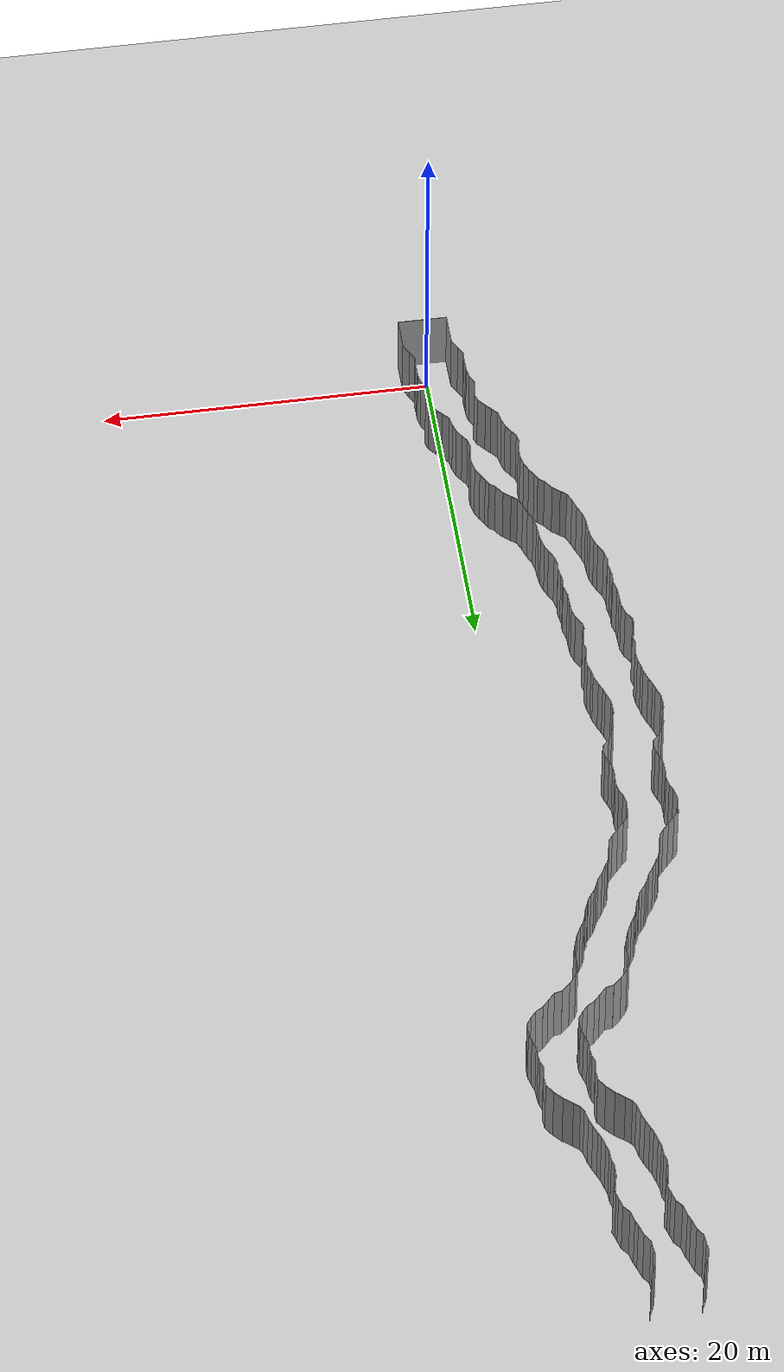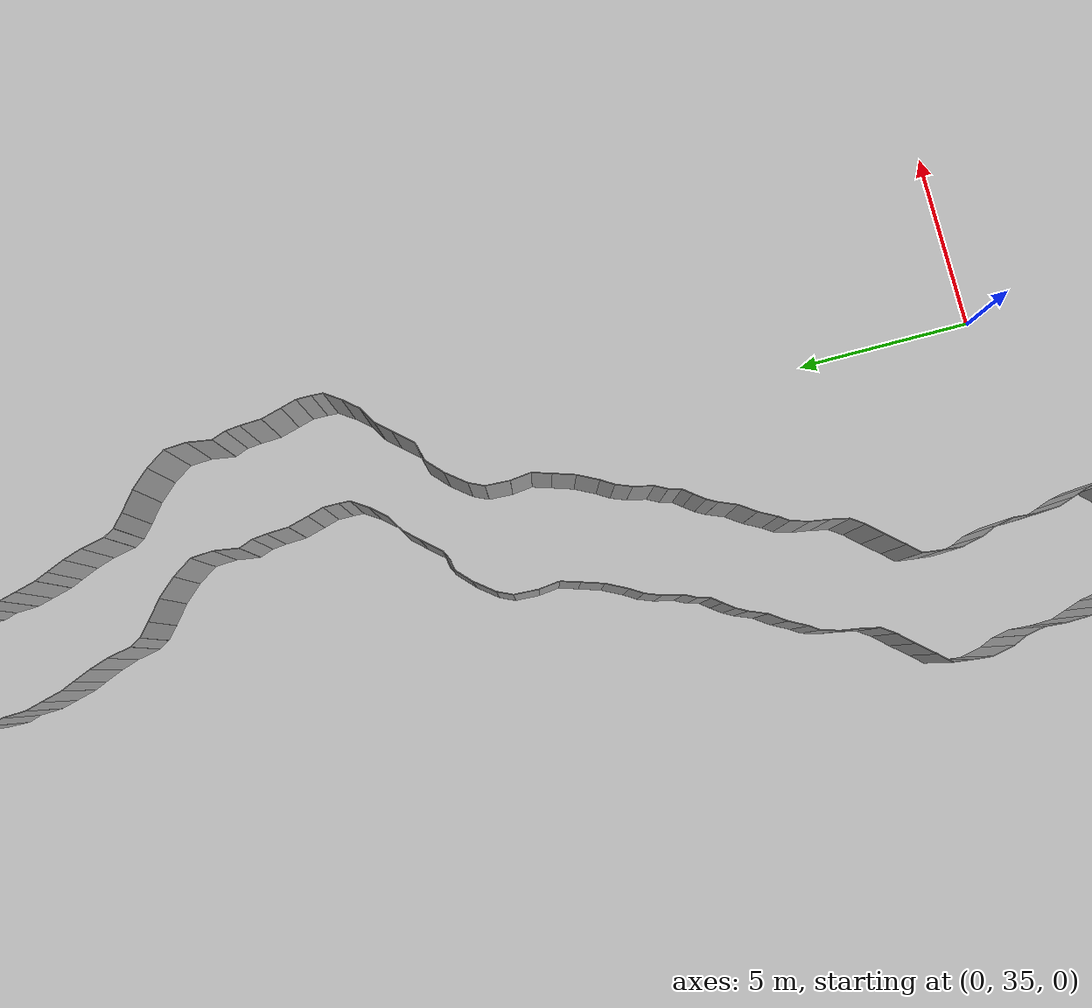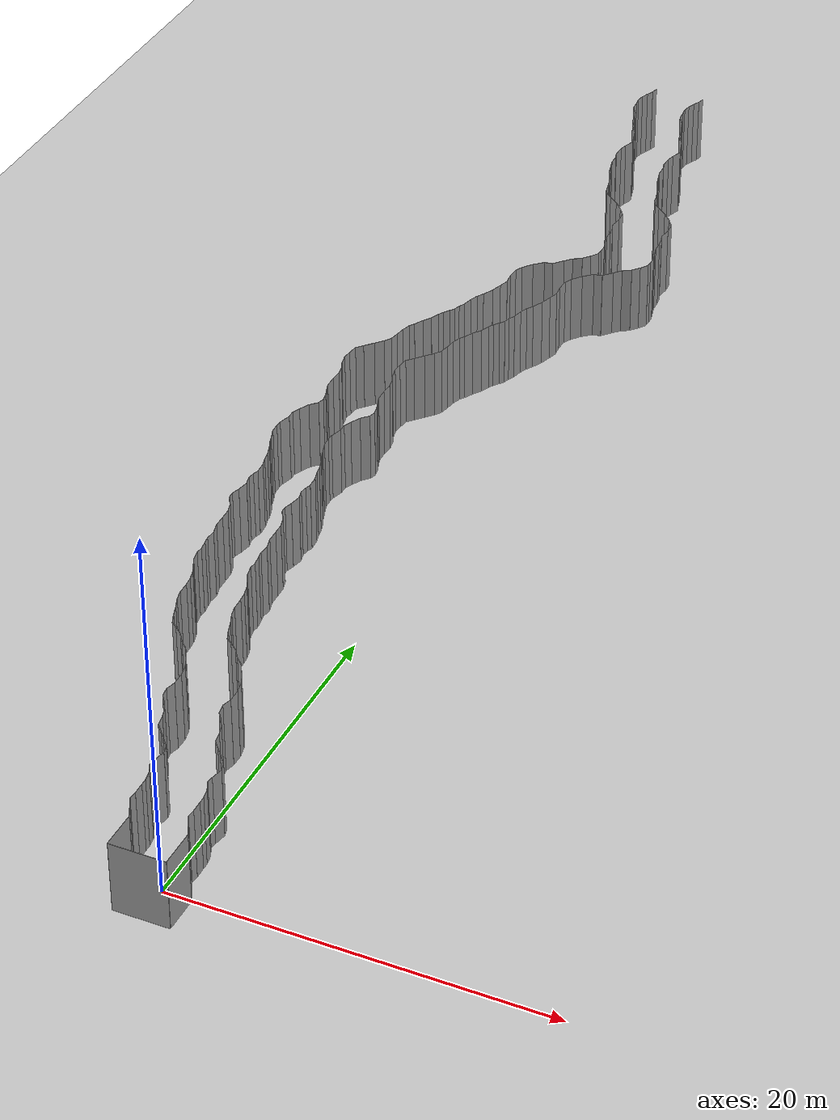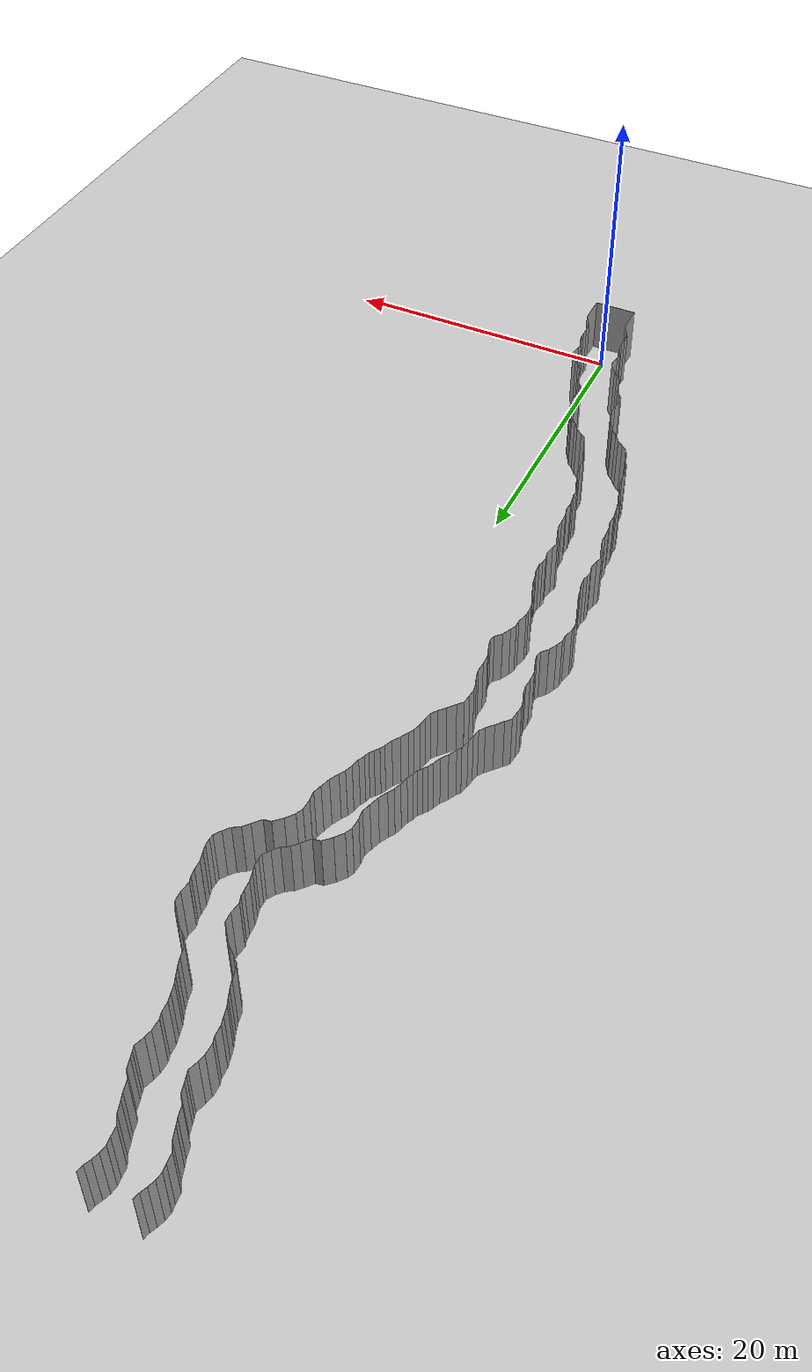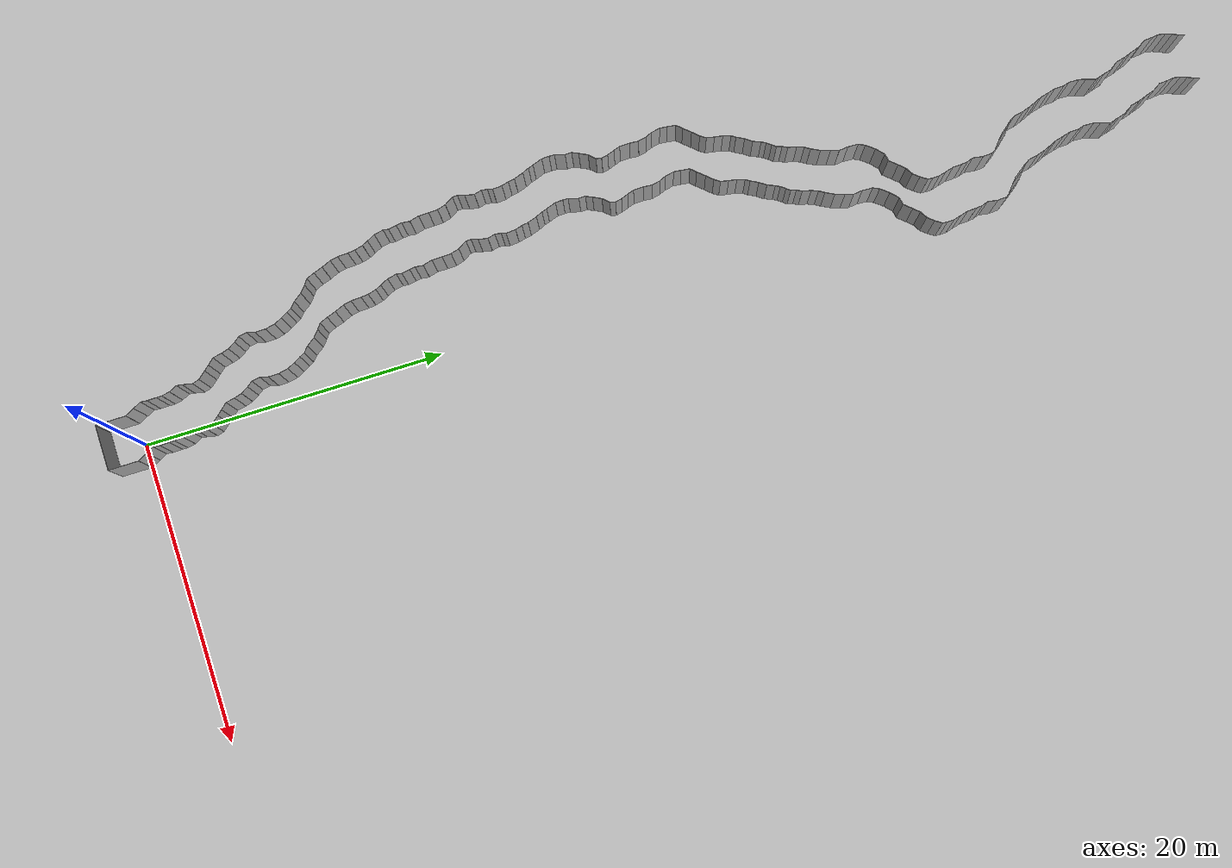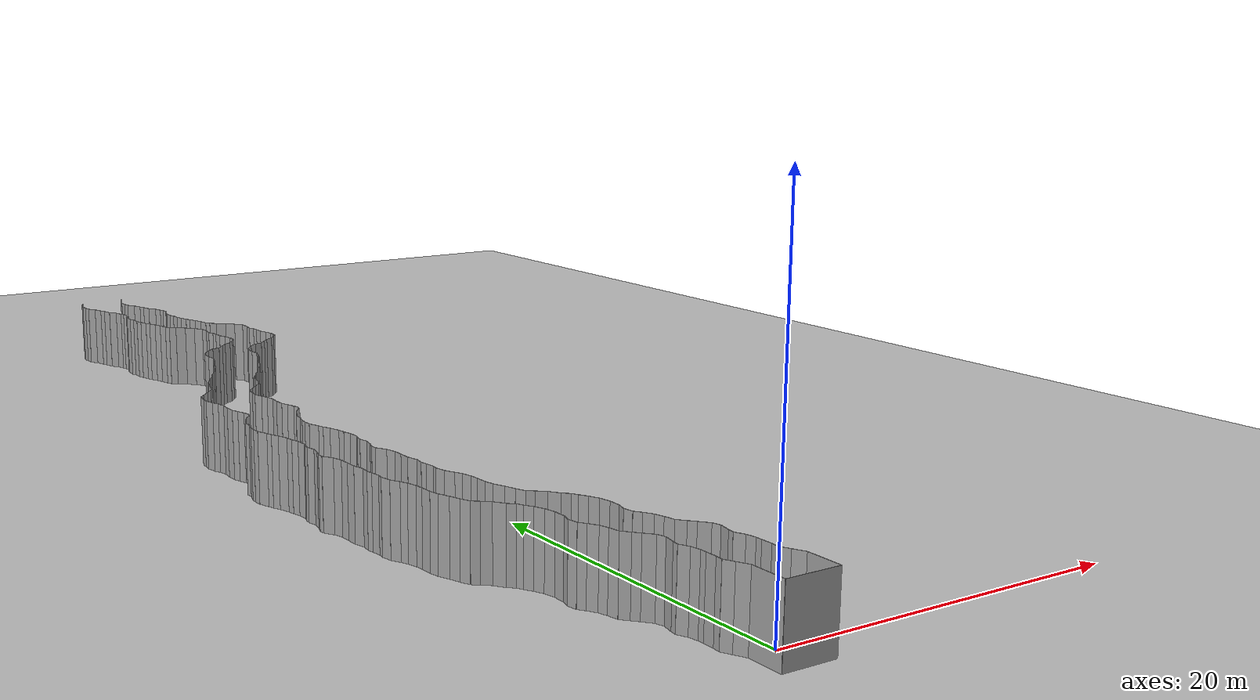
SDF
<sdf version="1.6">
 <world name="default">
  <light name="sun" type="directional">
   <pose>0 0 10 0 -0 0</pose>
   <diffuse>0.8 0.8 0.8 1</diffuse>
   <specular>0.2 0.2 0.2 1</specular>
   <attenuation>
    <range>1000</range>
    <constant>0.9</constant>
    <linear>0.01</linear>
    <quadratic>0.001</quadratic>
   </attenuation>
   <direction>-0.5 0.1 -0.9</direction>
  </light>
  <model name="ground_plane">
   <static>1</static>
   <link name="link">
    <collision name="collision">
     <geometry><plane><normal>0 0 1</normal><size>200 200</size></plane></geometry>
     <surface><friction><ode><mu>100</mu><mu2>50</mu2></ode></friction></surface>
    </collision>
    <visual name="visual">
     <cast_shadows>0</cast_shadows>
     <geometry><plane><normal>0 0 1</normal><size>200 200</size></plane></geometry>
     <material>
      <script><uri>file://media/materials/scripts/gazebo.material</uri><name>Gazebo/Grey</name></script>
     </material>
    </visual>
   </link>
   <pose>0 100 0 0 -0 0</pose>
  </model>
  <gravity>0 0 -9.8</gravity>
  <magnetic_field>6e-06 2.3e-05 -4.2e-05</magnetic_field>
  <atmosphere type="adiabatic"/>
  <physics default="0" name="default_physics" type="ode">
   <max_step_size>0.001</max_step_size>
   <real_time_factor>1</real_time_factor>
   <real_time_update_rate>1000</real_time_update_rate>
  </physics>
  <scene><ambient>0.4 0.4 0.4 1</ambient><background>0.7 0.7 0.7 1</background><shadows>1</shadows></scene>
  <spherical_coordinates>
   <surface_model>EARTH_WGS84</surface_model>
   <latitude_deg>0</latitude_deg>
   <longitude_deg>0</longitude_deg>
   <elevation>0</elevation>
   <heading_deg>0</heading_deg>
  </spherical_coordinates>
  <model name="wall_back">
   <static>1</static>
   <pose>0.0 -2 2 0.0 0 0.0</pose>
   <link name="link">
    <collision name="collision"><geometry><box><size>3 0.02 4</size></box></geometry></collision>
    <visual name="visual">
     <material>
      <script><name>Gazebo/Grey</name><uri>file://media/materials/scripts/gazebo.material</uri></script>
     </material>
     <geometry><box><size>3 0.02 4</size></box></geometry>
    </visual>
   </link>
  </model>
  <model name="wall_left">
   <static>1</static>
   <pose>1.5 -1 2 0 0 0.00</pose>
   <link name="link">
    <collision name="collision"><geometry><box><size>0.02 2 4</size></box></geometry></collision>
    <visual name="visual">
     <material>
      <script><name>Gazebo/Grey</name><uri>file://media/materials/scripts/gazebo.material</uri></script>
     </material>
     <geometry><box><size>0.02 2 4</size></box></geometry>
    </visual>
   </link>
  </model>
  <model name="wall_right">
   <static>1</static>
   <pose>-1.5 -1 2 0 0 0.00</pose>
   <link name="link">
    <collision name="collision"><geometry><box><size>0.02 2 4</size></box></geometry></collision>
    <visual name="visual">
     <material>
      <script><name>Gazebo/Grey</name><uri>file://media/materials/scripts/gazebo.material</uri></script>
     </material>
     <geometry><box><size>0.02 2 4</size></box></geometry>
    </visual>
   </link>
  </model>
  <model name="wall_0">
   <static>1</static>
   <pose>-1.6543823810586844 0.30656647983834645 2 0 0 0.46651175535888567</pose>
   <link name="link">
    <collision name="collision"><geometry><box><size>0.02 0.686489406012 4</size></box></geometry></collision>
    <visual name="visual">
     <material>
      <script><name>Gazebo/Grey</name><uri>file://media/materials/scripts/gazebo.material</uri></script>
     </material>
     <geometry><box><size>0.02 0.686489406012 4</size></box></geometry>
    </visual>
   </link>
  </model>
  <model name="wall_1">
   <static>1</static>
   <pose>1.3456176189413156 0.30656647983834645 2 0 0 0.46651175535888567</pose>
   <link name="link">
    <collision name="collision"><geometry><box><size>0.02 0.686489406012 4</size></box></geometry></collision>
    <visual name="visual">
     <material>
      <script><name>Gazebo/Grey</name><uri>file://media/materials/scripts/gazebo.material</uri></script>
     </material>
     <geometry><box><size>0.02 0.686489406012 4</size></box></geometry>
    </visual>
   </link>
  </model>
  <model name="wall_2">
   <static>1</static>
   <pose>-1.9452144958780733 0.8722627589688359 2 0 0 0.48467623624901895</pose>
   <link name="link">
    <collision name="collision"><geometry><box><size>0.02 0.585719327749 4</size></box></geometry></collision>
    <visual name="visual">
     <material>
      <script><name>Gazebo/Grey</name><uri>file://media/materials/scripts/gazebo.material</uri></script>
     </material>
     <geometry><box><size>0.02 0.585719327749 4</size></box></geometry>
    </visual>
   </link>
  </model>
  <model name="wall_3">
   <static>1</static>
   <pose>1.0547855041219267 0.8722627589688359 2 0 0 0.48467623624901895</pose>
   <link name="link">
    <collision name="collision"><geometry><box><size>0.02 0.585719327749 4</size></box></geometry></collision>
    <visual name="visual">
     <material>
      <script><name>Gazebo/Grey</name><uri>file://media/materials/scripts/gazebo.material</uri></script>
     </material>
     <geometry><box><size>0.02 0.585719327749 4</size></box></geometry>
    </visual>
   </link>
  </model>
  <model name="wall_4">
   <static>1</static>
   <pose>-2.059857094756395 1.3435047060668295 2 0 0 -0.10244951304842882</pose>
   <link name="link">
    <collision name="collision"><geometry><box><size>0.02 0.426460382116 4</size></box></geometry></collision>
    <visual name="visual">
     <material>
      <script><name>Gazebo/Grey</name><uri>file://media/materials/scripts/gazebo.material</uri></script>
     </material>
     <geometry><box><size>0.02 0.426460382116 4</size></box></geometry>
    </visual>
   </link>
  </model>
  <model name="wall_5">
   <static>1</static>
   <pose>0.9401429052436052 1.3435047060668295 2 0 0 -0.10244951304842882</pose>
   <link name="link">
    <collision name="collision"><geometry><box><size>0.02 0.426460382116 4</size></box></geometry></collision>
    <visual name="visual">
     <material>
      <script><name>Gazebo/Grey</name><uri>file://media/materials/scripts/gazebo.material</uri></script>
     </material>
     <geometry><box><size>0.02 0.426460382116 4</size></box></geometry>
    </visual>
   </link>
  </model>
  <model name="wall_6">
   <static>1</static>
   <pose>-2.0437863155778673 1.8674679967461443 2 0 0 0.01839245737626638</pose>
   <link name="link">
    <collision name="collision"><geometry><box><size>0.02 0.623807794399 4</size></box></geometry></collision>
    <visual name="visual">
     <material>
      <script><name>Gazebo/Grey</name><uri>file://media/materials/scripts/gazebo.material</uri></script>
     </material>
     <geometry><box><size>0.02 0.623807794399 4</size></box></geometry>
    </visual>
   </link>
  </model>
  <model name="wall_7">
   <static>1</static>
   <pose>0.9562136844221327 1.8674679967461443 2 0 0 0.01839245737626638</pose>
   <link name="link">
    <collision name="collision"><geometry><box><size>0.02 0.623807794399 4</size></box></geometry></collision>
    <visual name="visual">
     <material>
      <script><name>Gazebo/Grey</name><uri>file://media/materials/scripts/gazebo.material</uri></script>
     </material>
     <geometry><box><size>0.02 0.623807794399 4</size></box></geometry>
    </visual>
   </link>
  </model>
  <model name="wall_8">
   <static>1</static>
   <pose>-2.050072337990936 2.3553519176681665 2 0 0 0.0031225146184185324</pose>
   <link name="link">
    <collision name="collision"><geometry><box><size>0.02 0.352067272441 4</size></box></geometry></collision>
    <visual name="visual">
     <material>
      <script><name>Gazebo/Grey</name><uri>file://media/materials/scripts/gazebo.material</uri></script>
     </material>
     <geometry><box><size>0.02 0.352067272441 4</size></box></geometry>
    </visual>
   </link>
  </model>
  <model name="wall_9">
   <static>1</static>
   <pose>0.9499276620090642 2.3553519176681665 2 0 0 0.0031225146184185324</pose>
   <link name="link">
    <collision name="collision"><geometry><box><size>0.02 0.352067272441 4</size></box></geometry></collision>
    <visual name="visual">
     <material>
      <script><name>Gazebo/Grey</name><uri>file://media/materials/scripts/gazebo.material</uri></script>
     </material>
     <geometry><box><size>0.02 0.352067272441 4</size></box></geometry>
    </visual>
   </link>
  </model>
  <model name="wall_10">
   <static>1</static>
   <pose>-2.1010790889533584 2.7994131217400637 2 0 0 0.1860750211381766</pose>
   <link name="link">
    <collision name="collision"><geometry><box><size>0.02 0.545472838949 4</size></box></geometry></collision>
    <visual name="visual">
     <material>
      <script><name>Gazebo/Grey</name><uri>file://media/materials/scripts/gazebo.material</uri></script>
     </material>
     <geometry><box><size>0.02 0.545472838949 4</size></box></geometry>
    </visual>
   </link>
  </model>
  <model name="wall_11">
   <static>1</static>
   <pose>0.8989209110466416 2.7994131217400637 2 0 0 0.1860750211381766</pose>
   <link name="link">
    <collision name="collision"><geometry><box><size>0.02 0.545472838949 4</size></box></geometry></collision>
    <visual name="visual">
     <material>
      <script><name>Gazebo/Grey</name><uri>file://media/materials/scripts/gazebo.material</uri></script>
     </material>
     <geometry><box><size>0.02 0.545472838949 4</size></box></geometry>
    </visual>
   </link>
  </model>
  <model name="wall_12">
   <static>1</static>
   <pose>-2.279869380166036 3.3324791798309112 2 0 0 0.4509339707663869</pose>
   <link name="link">
    <collision name="collision"><geometry><box><size>0.02 0.588946036307 4</size></box></geometry></collision>
    <visual name="visual">
     <material>
      <script><name>Gazebo/Grey</name><uri>file://media/materials/scripts/gazebo.material</uri></script>
     </material>
     <geometry><box><size>0.02 0.588946036307 4</size></box></geometry>
    </visual>
   </link>
  </model>
  <model name="wall_13">
   <static>1</static>
   <pose>0.7201306198339639 3.3324791798309112 2 0 0 0.4509339707663869</pose>
   <link name="link">
    <collision name="collision"><geometry><box><size>0.02 0.588946036307 4</size></box></geometry></collision>
    <visual name="visual">
     <material>
      <script><name>Gazebo/Grey</name><uri>file://media/materials/scripts/gazebo.material</uri></script>
     </material>
     <geometry><box><size>0.02 0.588946036307 4</size></box></geometry>
    </visual>
   </link>
  </model>
  <model name="wall_14">
   <static>1</static>
   <pose>-2.383348714980828 3.7754929051992154 2 0 0 -0.1387499565541778</pose>
   <link name="link">
    <collision name="collision"><geometry><box><size>0.02 0.359406203325 4</size></box></geometry></collision>
    <visual name="visual">
     <material>
      <script><name>Gazebo/Grey</name><uri>file://media/materials/scripts/gazebo.material</uri></script>
     </material>
     <geometry><box><size>0.02 0.359406203325 4</size></box></geometry>
    </visual>
   </link>
  </model>
  <model name="wall_15">
   <static>1</static>
   <pose>0.6166512850191719 3.7754929051992154 2 0 0 -0.1387499565541778</pose>
   <link name="link">
    <collision name="collision"><geometry><box><size>0.02 0.359406203325 4</size></box></geometry></collision>
    <visual name="visual">
     <material>
      <script><name>Gazebo/Grey</name><uri>file://media/materials/scripts/gazebo.material</uri></script>
     </material>
     <geometry><box><size>0.02 0.359406203325 4</size></box></geometry>
    </visual>
   </link>
  </model>
  <model name="wall_16">
   <static>1</static>
   <pose>-2.290016331919445 4.279901721092762 2 0 0 -0.20677987608019407</pose>
   <link name="link">
    <collision name="collision"><geometry><box><size>0.02 0.66707609412 4</size></box></geometry></collision>
    <visual name="visual">
     <material>
      <script><name>Gazebo/Grey</name><uri>file://media/materials/scripts/gazebo.material</uri></script>
     </material>
     <geometry><box><size>0.02 0.66707609412 4</size></box></geometry>
    </visual>
   </link>
  </model>
  <model name="wall_17">
   <static>1</static>
   <pose>0.7099836680805551 4.279901721092762 2 0 0 -0.20677987608019407</pose>
   <link name="link">
    <collision name="collision"><geometry><box><size>0.02 0.66707609412 4</size></box></geometry></collision>
    <visual name="visual">
     <material>
      <script><name>Gazebo/Grey</name><uri>file://media/materials/scripts/gazebo.material</uri></script>
     </material>
     <geometry><box><size>0.02 0.66707609412 4</size></box></geometry>
    </visual>
   </link>
  </model>
  <model name="wall_18">
   <static>1</static>
   <pose>-2.2898368334641326 4.836894867763636 2 0 0 0.2879948910821208</pose>
   <link name="link">
    <collision name="collision"><geometry><box><size>0.02 0.480927704564 4</size></box></geometry></collision>
    <visual name="visual">
     <material>
      <script><name>Gazebo/Grey</name><uri>file://media/materials/scripts/gazebo.material</uri></script>
     </material>
     <geometry><box><size>0.02 0.480927704564 4</size></box></geometry>
    </visual>
   </link>
  </model>
  <model name="wall_19">
   <static>1</static>
   <pose>0.7101631665358674 4.836894867763636 2 0 0 0.2879948910821208</pose>
   <link name="link">
    <collision name="collision"><geometry><box><size>0.02 0.480927704564 4</size></box></geometry></collision>
    <visual name="visual">
     <material>
      <script><name>Gazebo/Grey</name><uri>file://media/materials/scripts/gazebo.material</uri></script>
     </material>
     <geometry><box><size>0.02 0.480927704564 4</size></box></geometry>
    </visual>
   </link>
  </model>
  <model name="wall_20">
   <static>1</static>
   <pose>-2.564620765072096 5.312654884640017 2 0 0 0.6998953788413514</pose>
   <link name="link">
    <collision name="collision"><geometry><box><size>0.02 0.641120463387 4</size></box></geometry></collision>
    <visual name="visual">
     <material>
      <script><name>Gazebo/Grey</name><uri>file://media/materials/scripts/gazebo.material</uri></script>
     </material>
     <geometry><box><size>0.02 0.641120463387 4</size></box></geometry>
    </visual>
   </link>
  </model>
  <model name="wall_21">
   <static>1</static>
   <pose>0.435379234927904 5.312654884640017 2 0 0 0.6998953788413514</pose>
   <link name="link">
    <collision name="collision"><geometry><box><size>0.02 0.641120463387 4</size></box></geometry></collision>
    <visual name="visual">
     <material>
      <script><name>Gazebo/Grey</name><uri>file://media/materials/scripts/gazebo.material</uri></script>
     </material>
     <geometry><box><size>0.02 0.641120463387 4</size></box></geometry>
    </visual>
   </link>
  </model>
  <model name="wall_22">
   <static>1</static>
   <pose>-2.919191703955924 5.72342609266741 2 0 0 0.7297084128582174</pose>
   <link name="link">
    <collision name="collision"><geometry><box><size>0.02 0.444267617596 4</size></box></geometry></collision>
    <visual name="visual">
     <material>
      <script><name>Gazebo/Grey</name><uri>file://media/materials/scripts/gazebo.material</uri></script>
     </material>
     <geometry><box><size>0.02 0.444267617596 4</size></box></geometry>
    </visual>
   </link>
  </model>
  <model name="wall_23">
   <static>1</static>
   <pose>0.08080829604407613 5.72342609266741 2 0 0 0.7297084128582174</pose>
   <link name="link">
    <collision name="collision"><geometry><box><size>0.02 0.444267617596 4</size></box></geometry></collision>
    <visual name="visual">
     <material>
      <script><name>Gazebo/Grey</name><uri>file://media/materials/scripts/gazebo.material</uri></script>
     </material>
     <geometry><box><size>0.02 0.444267617596 4</size></box></geometry>
    </visual>
   </link>
  </model>
  <model name="wall_24">
   <static>1</static>
   <pose>-3.2457934064803684 6.09286042455447 2 0 0 0.7192071707024089</pose>
   <link name="link">
    <collision name="collision"><geometry><box><size>0.02 0.541951496886 4</size></box></geometry></collision>
    <visual name="visual">
     <material>
      <script><name>Gazebo/Grey</name><uri>file://media/materials/scripts/gazebo.material</uri></script>
     </material>
     <geometry><box><size>0.02 0.541951496886 4</size></box></geometry>
    </visual>
   </link>
  </model>
  <model name="wall_25">
   <static>1</static>
   <pose>-0.2457934064803684 6.09286042455447 2 0 0 0.7192071707024089</pose>
   <link name="link">
    <collision name="collision"><geometry><box><size>0.02 0.541951496886 4</size></box></geometry></collision>
    <visual name="visual">
     <material>
      <script><name>Gazebo/Grey</name><uri>file://media/materials/scripts/gazebo.material</uri></script>
     </material>
     <geometry><box><size>0.02 0.541951496886 4</size></box></geometry>
    </visual>
   </link>
  </model>
  <model name="wall_26">
   <static>1</static>
   <pose>-3.482805525628354 6.596380888041652 2 0 0 0.19278637269477422</pose>
   <link name="link">
    <collision name="collision"><geometry><box><size>0.02 0.610627868023 4</size></box></geometry></collision>
    <visual name="visual">
     <material>
      <script><name>Gazebo/Grey</name><uri>file://media/materials/scripts/gazebo.material</uri></script>
     </material>
     <geometry><box><size>0.02 0.610627868023 4</size></box></geometry>
    </visual>
   </link>
  </model>
  <model name="wall_27">
   <static>1</static>
   <pose>-0.4828055256283541 6.596380888041652 2 0 0 0.19278637269477422</pose>
   <link name="link">
    <collision name="collision"><geometry><box><size>0.02 0.610627868023 4</size></box></geometry></collision>
    <visual name="visual">
     <material>
      <script><name>Gazebo/Grey</name><uri>file://media/materials/scripts/gazebo.material</uri></script>
     </material>
     <geometry><box><size>0.02 0.610627868023 4</size></box></geometry>
    </visual>
   </link>
  </model>
  <model name="wall_28">
   <static>1</static>
   <pose>-3.6148097615556565 7.144617172428788 2 0 0 0.28751875089007684</pose>
   <link name="link">
    <collision name="collision"><geometry><box><size>0.02 0.518438756003 4</size></box></geometry></collision>
    <visual name="visual">
     <material>
      <script><name>Gazebo/Grey</name><uri>file://media/materials/scripts/gazebo.material</uri></script>
     </material>
     <geometry><box><size>0.02 0.518438756003 4</size></box></geometry>
    </visual>
   </link>
  </model>
  <model name="wall_29">
   <static>1</static>
   <pose>-0.6148097615556565 7.144617172428788 2 0 0 0.28751875089007684</pose>
   <link name="link">
    <collision name="collision"><geometry><box><size>0.02 0.518438756003 4</size></box></geometry></collision>
    <visual name="visual">
     <material>
      <script><name>Gazebo/Grey</name><uri>file://media/materials/scripts/gazebo.material</uri></script>
     </material>
     <geometry><box><size>0.02 0.518438756003 4</size></box></geometry>
    </visual>
   </link>
  </model>
  <model name="wall_30">
   <static>1</static>
   <pose>-3.8345046086885612 7.635181016317983 2 0 0 0.5434400285841595</pose>
   <link name="link">
    <collision name="collision"><geometry><box><size>0.02 0.565429186924 4</size></box></geometry></collision>
    <visual name="visual">
     <material>
      <script><name>Gazebo/Grey</name><uri>file://media/materials/scripts/gazebo.material</uri></script>
     </material>
     <geometry><box><size>0.02 0.565429186924 4</size></box></geometry>
    </visual>
   </link>
  </model>
  <model name="wall_31">
   <static>1</static>
   <pose>-0.8345046086885612 7.635181016317983 2 0 0 0.5434400285841595</pose>
   <link name="link">
    <collision name="collision"><geometry><box><size>0.02 0.565429186924 4</size></box></geometry></collision>
    <visual name="visual">
     <material>
      <script><name>Gazebo/Grey</name><uri>file://media/materials/scripts/gazebo.material</uri></script>
     </material>
     <geometry><box><size>0.02 0.565429186924 4</size></box></geometry>
    </visual>
   </link>
  </model>
  <model name="wall_32">
   <static>1</static>
   <pose>-4.115288077113676 8.057760478986667 2 0 0 0.6404848788463845</pose>
   <link name="link">
    <collision name="collision"><geometry><box><size>0.02 0.450468404269 4</size></box></geometry></collision>
    <visual name="visual">
     <material>
      <script><name>Gazebo/Grey</name><uri>file://media/materials/scripts/gazebo.material</uri></script>
     </material>
     <geometry><box><size>0.02 0.450468404269 4</size></box></geometry>
    </visual>
   </link>
  </model>
  <model name="wall_33">
   <static>1</static>
   <pose>-1.115288077113676 8.057760478986667 2 0 0 0.6404848788463845</pose>
   <link name="link">
    <collision name="collision"><geometry><box><size>0.02 0.450468404269 4</size></box></geometry></collision>
    <visual name="visual">
     <material>
      <script><name>Gazebo/Grey</name><uri>file://media/materials/scripts/gazebo.material</uri></script>
     </material>
     <geometry><box><size>0.02 0.450468404269 4</size></box></geometry>
    </visual>
   </link>
  </model>
  <model name="wall_34">
   <static>1</static>
   <pose>-4.299435172877977 8.51320136878723 2 0 0 0.17836873913840587</pose>
   <link name="link">
    <collision name="collision"><geometry><box><size>0.02 0.558555265946 4</size></box></geometry></collision>
    <visual name="visual">
     <material>
      <script><name>Gazebo/Grey</name><uri>file://media/materials/scripts/gazebo.material</uri></script>
     </material>
     <geometry><box><size>0.02 0.558555265946 4</size></box></geometry>
    </visual>
   </link>
  </model>
  <model name="wall_35">
   <static>1</static>
   <pose>-1.2994351728779767 8.51320136878723 2 0 0 0.17836873913840587</pose>
   <link name="link">
    <collision name="collision"><geometry><box><size>0.02 0.558555265946 4</size></box></geometry></collision>
    <visual name="visual">
     <material>
      <script><name>Gazebo/Grey</name><uri>file://media/materials/scripts/gazebo.material</uri></script>
     </material>
     <geometry><box><size>0.02 0.558555265946 4</size></box></geometry>
    </visual>
   </link>
  </model>
  <model name="wall_36">
   <static>1</static>
   <pose>-4.2760185301588285 9.04758153323963 2 0 0 -0.27407297041161416</pose>
   <link name="link">
    <collision name="collision"><geometry><box><size>0.02 0.539191362106 4</size></box></geometry></collision>
    <visual name="visual">
     <material>
      <script><name>Gazebo/Grey</name><uri>file://media/materials/scripts/gazebo.material</uri></script>
     </material>
     <geometry><box><size>0.02 0.539191362106 4</size></box></geometry>
    </visual>
   </link>
  </model>
  <model name="wall_37">
   <static>1</static>
   <pose>-1.2760185301588285 9.04758153323963 2 0 0 -0.27407297041161416</pose>
   <link name="link">
    <collision name="collision"><geometry><box><size>0.02 0.539191362106 4</size></box></geometry></collision>
    <visual name="visual">
     <material>
      <script><name>Gazebo/Grey</name><uri>file://media/materials/scripts/gazebo.material</uri></script>
     </material>
     <geometry><box><size>0.02 0.539191362106 4</size></box></geometry>
    </visual>
   </link>
  </model>
  <model name="wall_38">
   <static>1</static>
   <pose>-4.20504366651556 9.652917953593123 2 0 0 0.005761754508568655</pose>
   <link name="link">
    <collision name="collision"><geometry><box><size>0.02 0.691617458791 4</size></box></geometry></collision>
    <visual name="visual">
     <material>
      <script><name>Gazebo/Grey</name><uri>file://media/materials/scripts/gazebo.material</uri></script>
     </material>
     <geometry><box><size>0.02 0.691617458791 4</size></box></geometry>
    </visual>
   </link>
  </model>
  <model name="wall_39">
   <static>1</static>
   <pose>-1.20504366651556 9.652917953593123 2 0 0 0.005761754508568655</pose>
   <link name="link">
    <collision name="collision"><geometry><box><size>0.02 0.691617458791 4</size></box></geometry></collision>
    <visual name="visual">
     <material>
      <script><name>Gazebo/Grey</name><uri>file://media/materials/scripts/gazebo.material</uri></script>
     </material>
     <geometry><box><size>0.02 0.691617458791 4</size></box></geometry>
    </visual>
   </link>
  </model>
  <model name="wall_40">
   <static>1</static>
   <pose>-4.274500966864753 10.314746966604584 2 0 0 0.21032168698291834</pose>
   <link name="link">
    <collision name="collision"><geometry><box><size>0.02 0.646293905643 4</size></box></geometry></collision>
    <visual name="visual">
     <material>
      <script><name>Gazebo/Grey</name><uri>file://media/materials/scripts/gazebo.material</uri></script>
     </material>
     <geometry><box><size>0.02 0.646293905643 4</size></box></geometry>
    </visual>
   </link>
  </model>
  <model name="wall_41">
   <static>1</static>
   <pose>-1.2745009668647533 10.314746966604584 2 0 0 0.21032168698291834</pose>
   <link name="link">
    <collision name="collision"><geometry><box><size>0.02 0.646293905643 4</size></box></geometry></collision>
    <visual name="visual">
     <material>
      <script><name>Gazebo/Grey</name><uri>file://media/materials/scripts/gazebo.material</uri></script>
     </material>
     <geometry><box><size>0.02 0.646293905643 4</size></box></geometry>
    </visual>
   </link>
  </model>
  <model name="wall_42">
   <static>1</static>
   <pose>-4.457773014037533 10.886065462250867 2 0 0 0.42586488387103183</pose>
   <link name="link">
    <collision name="collision"><geometry><box><size>0.02 0.560662301275 4</size></box></geometry></collision>
    <visual name="visual">
     <material>
      <script><name>Gazebo/Grey</name><uri>file://media/materials/scripts/gazebo.material</uri></script>
     </material>
     <geometry><box><size>0.02 0.560662301275 4</size></box></geometry>
    </visual>
   </link>
  </model>
  <model name="wall_43">
   <static>1</static>
   <pose>-1.4577730140375333 10.886065462250867 2 0 0 0.42586488387103183</pose>
   <link name="link">
    <collision name="collision"><geometry><box><size>0.02 0.560662301275 4</size></box></geometry></collision>
    <visual name="visual">
     <material>
      <script><name>Gazebo/Grey</name><uri>file://media/materials/scripts/gazebo.material</uri></script>
     </material>
     <geometry><box><size>0.02 0.560662301275 4</size></box></geometry>
    </visual>
   </link>
  </model>
  <model name="wall_44">
   <static>1</static>
   <pose>-4.703960582407086 11.35962647889364 2 0 0 0.5384607656495747</pose>
   <link name="link">
    <collision name="collision"><geometry><box><size>0.02 0.508488732725 4</size></box></geometry></collision>
    <visual name="visual">
     <material>
      <script><name>Gazebo/Grey</name><uri>file://media/materials/scripts/gazebo.material</uri></script>
     </material>
     <geometry><box><size>0.02 0.508488732725 4</size></box></geometry>
    </visual>
   </link>
  </model>
  <model name="wall_45">
   <static>1</static>
   <pose>-1.7039605824070856 11.35962647889364 2 0 0 0.5384607656495747</pose>
   <link name="link">
    <collision name="collision"><geometry><box><size>0.02 0.508488732725 4</size></box></geometry></collision>
    <visual name="visual">
     <material>
      <script><name>Gazebo/Grey</name><uri>file://media/materials/scripts/gazebo.material</uri></script>
     </material>
     <geometry><box><size>0.02 0.508488732725 4</size></box></geometry>
    </visual>
   </link>
  </model>
  <model name="wall_46">
   <static>1</static>
   <pose>-4.918099443545411 11.743242715882806 2 0 0 0.46888166544557536</pose>
   <link name="link">
    <collision name="collision"><geometry><box><size>0.02 0.370703895905 4</size></box></geometry></collision>
    <visual name="visual">
     <material>
      <script><name>Gazebo/Grey</name><uri>file://media/materials/scripts/gazebo.material</uri></script>
     </material>
     <geometry><box><size>0.02 0.370703895905 4</size></box></geometry>
    </visual>
   </link>
  </model>
  <model name="wall_47">
   <static>1</static>
   <pose>-1.9180994435454108 11.743242715882806 2 0 0 0.46888166544557536</pose>
   <link name="link">
    <collision name="collision"><geometry><box><size>0.02 0.370703895905 4</size></box></geometry></collision>
    <visual name="visual">
     <material>
      <script><name>Gazebo/Grey</name><uri>file://media/materials/scripts/gazebo.material</uri></script>
     </material>
     <geometry><box><size>0.02 0.370703895905 4</size></box></geometry>
    </visual>
   </link>
  </model>
  <model name="wall_48">
   <static>1</static>
   <pose>-5.179390324439873 12.066083320564976 2 0 0 0.8451417917808436</pose>
   <link name="link">
    <collision name="collision"><geometry><box><size>0.02 0.47464414453 4</size></box></geometry></collision>
    <visual name="visual">
     <material>
      <script><name>Gazebo/Grey</name><uri>file://media/materials/scripts/gazebo.material</uri></script>
     </material>
     <geometry><box><size>0.02 0.47464414453 4</size></box></geometry>
    </visual>
   </link>
  </model>
  <model name="wall_49">
   <static>1</static>
   <pose>-2.179390324439873 12.066083320564976 2 0 0 0.8451417917808436</pose>
   <link name="link">
    <collision name="collision"><geometry><box><size>0.02 0.47464414453 4</size></box></geometry></collision>
    <visual name="visual">
     <material>
      <script><name>Gazebo/Grey</name><uri>file://media/materials/scripts/gazebo.material</uri></script>
     </material>
     <geometry><box><size>0.02 0.47464414453 4</size></box></geometry>
    </visual>
   </link>
  </model>
  <model name="wall_50">
   <static>1</static>
   <pose>-5.551896465735448 12.496326528862921 2 0 0 0.6206186792407631</pose>
   <link name="link">
    <collision name="collision"><geometry><box><size>0.02 0.670544521075 4</size></box></geometry></collision>
    <visual name="visual">
     <material>
      <script><name>Gazebo/Grey</name><uri>file://media/materials/scripts/gazebo.material</uri></script>
     </material>
     <geometry><box><size>0.02 0.670544521075 4</size></box></geometry>
    </visual>
   </link>
  </model>
  <model name="wall_51">
   <static>1</static>
   <pose>-2.5518964657354477 12.496326528862921 2 0 0 0.6206186792407631</pose>
   <link name="link">
    <collision name="collision"><geometry><box><size>0.02 0.670544521075 4</size></box></geometry></collision>
    <visual name="visual">
     <material>
      <script><name>Gazebo/Grey</name><uri>file://media/materials/scripts/gazebo.material</uri></script>
     </material>
     <geometry><box><size>0.02 0.670544521075 4</size></box></geometry>
    </visual>
   </link>
  </model>
  <model name="wall_52">
   <static>1</static>
   <pose>-5.964303892062197 12.953702459686623 2 0 0 0.8668177658218559</pose>
   <link name="link">
    <collision name="collision"><geometry><box><size>0.02 0.570487605197 4</size></box></geometry></collision>
    <visual name="visual">
     <material>
      <script><name>Gazebo/Grey</name><uri>file://media/materials/scripts/gazebo.material</uri></script>
     </material>
     <geometry><box><size>0.02 0.570487605197 4</size></box></geometry>
    </visual>
   </link>
  </model>
  <model name="wall_53">
   <static>1</static>
   <pose>-2.9643038920621967 12.953702459686623 2 0 0 0.8668177658218559</pose>
   <link name="link">
    <collision name="collision"><geometry><box><size>0.02 0.570487605197 4</size></box></geometry></collision>
    <visual name="visual">
     <material>
      <script><name>Gazebo/Grey</name><uri>file://media/materials/scripts/gazebo.material</uri></script>
     </material>
     <geometry><box><size>0.02 0.570487605197 4</size></box></geometry>
    </visual>
   </link>
  </model>
  <model name="wall_54">
   <static>1</static>
   <pose>-6.357036600522708 13.272945342648471 2 0 0 0.9159189311959149</pose>
   <link name="link">
    <collision name="collision"><geometry><box><size>0.02 0.442047760074 4</size></box></geometry></collision>
    <visual name="visual">
     <material>
      <script><name>Gazebo/Grey</name><uri>file://media/materials/scripts/gazebo.material</uri></script>
     </material>
     <geometry><box><size>0.02 0.442047760074 4</size></box></geometry>
    </visual>
   </link>
  </model>
  <model name="wall_55">
   <static>1</static>
   <pose>-3.357036600522708 13.272945342648471 2 0 0 0.9159189311959149</pose>
   <link name="link">
    <collision name="collision"><geometry><box><size>0.02 0.442047760074 4</size></box></geometry></collision>
    <visual name="visual">
     <material>
      <script><name>Gazebo/Grey</name><uri>file://media/materials/scripts/gazebo.material</uri></script>
     </material>
     <geometry><box><size>0.02 0.442047760074 4</size></box></geometry>
    </visual>
   </link>
  </model>
  <model name="wall_56">
   <static>1</static>
   <pose>-6.646114318915432 13.67549192420865 2 0 0 0.4015820331990404</pose>
   <link name="link">
    <collision name="collision"><geometry><box><size>0.02 0.582174256631 4</size></box></geometry></collision>
    <visual name="visual">
     <material>
      <script><name>Gazebo/Grey</name><uri>file://media/materials/scripts/gazebo.material</uri></script>
     </material>
     <geometry><box><size>0.02 0.582174256631 4</size></box></geometry>
    </visual>
   </link>
  </model>
  <model name="wall_57">
   <static>1</static>
   <pose>-3.6461143189154317 13.67549192420865 2 0 0 0.4015820331990404</pose>
   <link name="link">
    <collision name="collision"><geometry><box><size>0.02 0.582174256631 4</size></box></geometry></collision>
    <visual name="visual">
     <material>
      <script><name>Gazebo/Grey</name><uri>file://media/materials/scripts/gazebo.material</uri></script>
     </material>
     <geometry><box><size>0.02 0.582174256631 4</size></box></geometry>
    </visual>
   </link>
  </model>
  <model name="wall_58">
   <static>1</static>
   <pose>-6.857996356947405 14.241056013758298 2 0 0 0.3183957100025487</pose>
   <link name="link">
    <collision name="collision"><geometry><box><size>0.02 0.626771781245 4</size></box></geometry></collision>
    <visual name="visual">
     <material>
      <script><name>Gazebo/Grey</name><uri>file://media/materials/scripts/gazebo.material</uri></script>
     </material>
     <geometry><box><size>0.02 0.626771781245 4</size></box></geometry>
    </visual>
   </link>
  </model>
  <model name="wall_59">
   <static>1</static>
   <pose>-3.857996356947405 14.241056013758298 2 0 0 0.3183957100025487</pose>
   <link name="link">
    <collision name="collision"><geometry><box><size>0.02 0.626771781245 4</size></box></geometry></collision>
    <visual name="visual">
     <material>
      <script><name>Gazebo/Grey</name><uri>file://media/materials/scripts/gazebo.material</uri></script>
     </material>
     <geometry><box><size>0.02 0.626771781245 4</size></box></geometry>
    </visual>
   </link>
  </model>
  <model name="wall_60">
   <static>1</static>
   <pose>-7.0833512909204295 14.845704658360427 2 0 0 0.39292776241886906</pose>
   <link name="link">
    <collision name="collision"><geometry><box><size>0.02 0.664681854426 4</size></box></geometry></collision>
    <visual name="visual">
     <material>
      <script><name>Gazebo/Grey</name><uri>file://media/materials/scripts/gazebo.material</uri></script>
     </material>
     <geometry><box><size>0.02 0.664681854426 4</size></box></geometry>
    </visual>
   </link>
  </model>
  <model name="wall_61">
   <static>1</static>
   <pose>-4.0833512909204295 14.845704658360427 2 0 0 0.39292776241886906</pose>
   <link name="link">
    <collision name="collision"><geometry><box><size>0.02 0.664681854426 4</size></box></geometry></collision>
    <visual name="visual">
     <material>
      <script><name>Gazebo/Grey</name><uri>file://media/materials/scripts/gazebo.material</uri></script>
     </material>
     <geometry><box><size>0.02 0.664681854426 4</size></box></geometry>
    </visual>
   </link>
  </model>
  <model name="wall_62">
   <static>1</static>
   <pose>-7.268294154239975 15.416405111375003 2 0 0 0.2153933452892111</pose>
   <link name="link">
    <collision name="collision"><geometry><box><size>0.02 0.539847714358 4</size></box></geometry></collision>
    <visual name="visual">
     <material>
      <script><name>Gazebo/Grey</name><uri>file://media/materials/scripts/gazebo.material</uri></script>
     </material>
     <geometry><box><size>0.02 0.539847714358 4</size></box></geometry>
    </visual>
   </link>
  </model>
  <model name="wall_63">
   <static>1</static>
   <pose>-4.268294154239975 15.416405111375003 2 0 0 0.2153933452892111</pose>
   <link name="link">
    <collision name="collision"><geometry><box><size>0.02 0.539847714358 4</size></box></geometry></collision>
    <visual name="visual">
     <material>
      <script><name>Gazebo/Grey</name><uri>file://media/materials/scripts/gazebo.material</uri></script>
     </material>
     <geometry><box><size>0.02 0.539847714358 4</size></box></geometry>
    </visual>
   </link>
  </model>
  <model name="wall_64">
   <static>1</static>
   <pose>-7.339893843065096 16.02458330863012 2 0 0 0.04035179007164962</pose>
   <link name="link">
    <collision name="collision"><geometry><box><size>0.02 0.68954457066 4</size></box></geometry></collision>
    <visual name="visual">
     <material>
      <script><name>Gazebo/Grey</name><uri>file://media/materials/scripts/gazebo.material</uri></script>
     </material>
     <geometry><box><size>0.02 0.68954457066 4</size></box></geometry>
    </visual>
   </link>
  </model>
  <model name="wall_65">
   <static>1</static>
   <pose>-4.339893843065096 16.02458330863012 2 0 0 0.04035179007164962</pose>
   <link name="link">
    <collision name="collision"><geometry><box><size>0.02 0.68954457066 4</size></box></geometry></collision>
    <visual name="visual">
     <material>
      <script><name>Gazebo/Grey</name><uri>file://media/materials/scripts/gazebo.material</uri></script>
     </material>
     <geometry><box><size>0.02 0.68954457066 4</size></box></geometry>
    </visual>
   </link>
  </model>
  <model name="wall_66">
   <static>1</static>
   <pose>-7.379220181064299 16.60984750586899 2 0 0 0.10517866128709</pose>
   <link name="link">
    <collision name="collision"><geometry><box><size>0.02 0.484221020573 4</size></box></geometry></collision>
    <visual name="visual">
     <material>
      <script><name>Gazebo/Grey</name><uri>file://media/materials/scripts/gazebo.material</uri></script>
     </material>
     <geometry><box><size>0.02 0.484221020573 4</size></box></geometry>
    </visual>
   </link>
  </model>
  <model name="wall_67">
   <static>1</static>
   <pose>-4.379220181064299 16.60984750586899 2 0 0 0.10517866128709</pose>
   <link name="link">
    <collision name="collision"><geometry><box><size>0.02 0.484221020573 4</size></box></geometry></collision>
    <visual name="visual">
     <material>
      <script><name>Gazebo/Grey</name><uri>file://media/materials/scripts/gazebo.material</uri></script>
     </material>
     <geometry><box><size>0.02 0.484221020573 4</size></box></geometry>
    </visual>
   </link>
  </model>
  <model name="wall_68">
   <static>1</static>
   <pose>-7.476948264503303 17.125807262545347 2 0 0 0.25695822527983436</pose>
   <link name="link">
    <collision name="collision"><geometry><box><size>0.02 0.569057987974 4</size></box></geometry></collision>
    <visual name="visual">
     <material>
      <script><name>Gazebo/Grey</name><uri>file://media/materials/scripts/gazebo.material</uri></script>
     </material>
     <geometry><box><size>0.02 0.569057987974 4</size></box></geometry>
    </visual>
   </link>
  </model>
  <model name="wall_69">
   <static>1</static>
   <pose>-4.476948264503303 17.125807262545347 2 0 0 0.25695822527983436</pose>
   <link name="link">
    <collision name="collision"><geometry><box><size>0.02 0.569057987974 4</size></box></geometry></collision>
    <visual name="visual">
     <material>
      <script><name>Gazebo/Grey</name><uri>file://media/materials/scripts/gazebo.material</uri></script>
     </material>
     <geometry><box><size>0.02 0.569057987974 4</size></box></geometry>
    </visual>
   </link>
  </model>
  <model name="wall_70">
   <static>1</static>
   <pose>-7.6383461126709165 17.594561762734372 2 0 0 0.43133800648701814</pose>
   <link name="link">
    <collision name="collision"><geometry><box><size>0.02 0.426168609065 4</size></box></geometry></collision>
    <visual name="visual">
     <material>
      <script><name>Gazebo/Grey</name><uri>file://media/materials/scripts/gazebo.material</uri></script>
     </material>
     <geometry><box><size>0.02 0.426168609065 4</size></box></geometry>
    </visual>
   </link>
  </model>
  <model name="wall_71">
   <static>1</static>
   <pose>-4.6383461126709165 17.594561762734372 2 0 0 0.43133800648701814</pose>
   <link name="link">
    <collision name="collision"><geometry><box><size>0.02 0.426168609065 4</size></box></geometry></collision>
    <visual name="visual">
     <material>
      <script><name>Gazebo/Grey</name><uri>file://media/materials/scripts/gazebo.material</uri></script>
     </material>
     <geometry><box><size>0.02 0.426168609065 4</size></box></geometry>
    </visual>
   </link>
  </model>
  <model name="wall_72">
   <static>1</static>
   <pose>-7.859079595083798 18.051267998944404 2 0 0 0.46387960950541135</pose>
   <link name="link">
    <collision name="collision"><geometry><box><size>0.02 0.588464808912 4</size></box></geometry></collision>
    <visual name="visual">
     <material>
      <script><name>Gazebo/Grey</name><uri>file://media/materials/scripts/gazebo.material</uri></script>
     </material>
     <geometry><box><size>0.02 0.588464808912 4</size></box></geometry>
    </visual>
   </link>
  </model>
  <model name="wall_73">
   <static>1</static>
   <pose>-4.859079595083798 18.051267998944404 2 0 0 0.46387960950541135</pose>
   <link name="link">
    <collision name="collision"><geometry><box><size>0.02 0.588464808912 4</size></box></geometry></collision>
    <visual name="visual">
     <material>
      <script><name>Gazebo/Grey</name><uri>file://media/materials/scripts/gazebo.material</uri></script>
     </material>
     <geometry><box><size>0.02 0.588464808912 4</size></box></geometry>
    </visual>
   </link>
  </model>
  <model name="wall_74">
   <static>1</static>
   <pose>-8.054942996099062 18.622079364378454 2 0 0 0.20576664837579636</pose>
   <link name="link">
    <collision name="collision"><geometry><box><size>0.02 0.628605539384 4</size></box></geometry></collision>
    <visual name="visual">
     <material>
      <script><name>Gazebo/Grey</name><uri>file://media/materials/scripts/gazebo.material</uri></script>
     </material>
     <geometry><box><size>0.02 0.628605539384 4</size></box></geometry>
    </visual>
   </link>
  </model>
  <model name="wall_75">
   <static>1</static>
   <pose>-5.0549429960990615 18.622079364378454 2 0 0 0.20576664837579636</pose>
   <link name="link">
    <collision name="collision"><geometry><box><size>0.02 0.628605539384 4</size></box></geometry></collision>
    <visual name="visual">
     <material>
      <script><name>Gazebo/Grey</name><uri>file://media/materials/scripts/gazebo.material</uri></script>
     </material>
     <geometry><box><size>0.02 0.628605539384 4</size></box></geometry>
    </visual>
   </link>
  </model>
  <model name="wall_76">
   <static>1</static>
   <pose>-8.094000291962661 19.10459928244877 2 0 0 -0.1429176120640637</pose>
   <link name="link">
    <collision name="collision"><geometry><box><size>0.02 0.3532969479 4</size></box></geometry></collision>
    <visual name="visual">
     <material>
      <script><name>Gazebo/Grey</name><uri>file://media/materials/scripts/gazebo.material</uri></script>
     </material>
     <geometry><box><size>0.02 0.3532969479 4</size></box></geometry>
    </visual>
   </link>
  </model>
  <model name="wall_77">
   <static>1</static>
   <pose>-5.0940002919626615 19.10459928244877 2 0 0 -0.1429176120640637</pose>
   <link name="link">
    <collision name="collision"><geometry><box><size>0.02 0.3532969479 4</size></box></geometry></collision>
    <visual name="visual">
     <material>
      <script><name>Gazebo/Grey</name><uri>file://media/materials/scripts/gazebo.material</uri></script>
     </material>
     <geometry><box><size>0.02 0.3532969479 4</size></box></geometry>
    </visual>
   </link>
  </model>
  <model name="wall_78">
   <static>1</static>
   <pose>-8.109329465776387 19.55113375653813 2 0 0 0.14794109622288584</pose>
   <link name="link">
    <collision name="collision"><geometry><box><size>0.02 0.549374995959 4</size></box></geometry></collision>
    <visual name="visual">
     <material>
      <script><name>Gazebo/Grey</name><uri>file://media/materials/scripts/gazebo.material</uri></script>
     </material>
     <geometry><box><size>0.02 0.549374995959 4</size></box></geometry>
    </visual>
   </link>
  </model>
  <model name="wall_79">
   <static>1</static>
   <pose>-5.109329465776387 19.55113375653813 2 0 0 0.14794109622288584</pose>
   <link name="link">
    <collision name="collision"><geometry><box><size>0.02 0.549374995959 4</size></box></geometry></collision>
    <visual name="visual">
     <material>
      <script><name>Gazebo/Grey</name><uri>file://media/materials/scripts/gazebo.material</uri></script>
     </material>
     <geometry><box><size>0.02 0.549374995959 4</size></box></geometry>
    </visual>
   </link>
  </model>
  <model name="wall_80">
   <static>1</static>
   <pose>-8.180743322352622 20.010506009818247 2 0 0 0.16329990901989272</pose>
   <link name="link">
    <collision name="collision"><geometry><box><size>0.02 0.38043171761 4</size></box></geometry></collision>
    <visual name="visual">
     <material>
      <script><name>Gazebo/Grey</name><uri>file://media/materials/scripts/gazebo.material</uri></script>
     </material>
     <geometry><box><size>0.02 0.38043171761 4</size></box></geometry>
    </visual>
   </link>
  </model>
  <model name="wall_81">
   <static>1</static>
   <pose>-5.1807433223526225 20.010506009818247 2 0 0 0.16329990901989272</pose>
   <link name="link">
    <collision name="collision"><geometry><box><size>0.02 0.38043171761 4</size></box></geometry></collision>
    <visual name="visual">
     <material>
      <script><name>Gazebo/Grey</name><uri>file://media/materials/scripts/gazebo.material</uri></script>
     </material>
     <geometry><box><size>0.02 0.38043171761 4</size></box></geometry>
    </visual>
   </link>
  </model>
  <model name="wall_82">
   <static>1</static>
   <pose>-8.181710078997972 20.464378614292592 2 0 0 -0.11207172929041374</pose>
   <link name="link">
    <collision name="collision"><geometry><box><size>0.02 0.535735607917 4</size></box></geometry></collision>
    <visual name="visual">
     <material>
      <script><name>Gazebo/Grey</name><uri>file://media/materials/scripts/gazebo.material</uri></script>
     </material>
     <geometry><box><size>0.02 0.535735607917 4</size></box></geometry>
    </visual>
   </link>
  </model>
  <model name="wall_83">
   <static>1</static>
   <pose>-5.1817100789979715 20.464378614292592 2 0 0 -0.11207172929041374</pose>
   <link name="link">
    <collision name="collision"><geometry><box><size>0.02 0.535735607917 4</size></box></geometry></collision>
    <visual name="visual">
     <material>
      <script><name>Gazebo/Grey</name><uri>file://media/materials/scripts/gazebo.material</uri></script>
     </material>
     <geometry><box><size>0.02 0.535735607917 4</size></box></geometry>
    </visual>
   </link>
  </model>
  <model name="wall_84">
   <static>1</static>
   <pose>-8.234010232352365 21.047139643242097 2 0 0 0.25421596916085887</pose>
   <link name="link">
    <collision name="collision"><geometry><box><size>0.02 0.654171954259 4</size></box></geometry></collision>
    <visual name="visual">
     <material>
      <script><name>Gazebo/Grey</name><uri>file://media/materials/scripts/gazebo.material</uri></script>
     </material>
     <geometry><box><size>0.02 0.654171954259 4</size></box></geometry>
    </visual>
   </link>
  </model>
  <model name="wall_85">
   <static>1</static>
   <pose>-5.2340102323523645 21.047139643242097 2 0 0 0.25421596916085887</pose>
   <link name="link">
    <collision name="collision"><geometry><box><size>0.02 0.654171954259 4</size></box></geometry></collision>
    <visual name="visual">
     <material>
      <script><name>Gazebo/Grey</name><uri>file://media/materials/scripts/gazebo.material</uri></script>
     </material>
     <geometry><box><size>0.02 0.654171954259 4</size></box></geometry>
    </visual>
   </link>
  </model>
  <model name="wall_86">
   <static>1</static>
   <pose>-8.322876717147118 21.69940661886569 2 0 0 0.01968425837181892</pose>
   <link name="link">
    <collision name="collision"><geometry><box><size>0.02 0.67151667431 4</size></box></geometry></collision>
    <visual name="visual">
     <material>
      <script><name>Gazebo/Grey</name><uri>file://media/materials/scripts/gazebo.material</uri></script>
     </material>
     <geometry><box><size>0.02 0.67151667431 4</size></box></geometry>
    </visual>
   </link>
  </model>
  <model name="wall_87">
   <static>1</static>
   <pose>-5.322876717147118 21.69940661886569 2 0 0 0.01968425837181892</pose>
   <link name="link">
    <collision name="collision"><geometry><box><size>0.02 0.67151667431 4</size></box></geometry></collision>
    <visual name="visual">
     <material>
      <script><name>Gazebo/Grey</name><uri>file://media/materials/scripts/gazebo.material</uri></script>
     </material>
     <geometry><box><size>0.02 0.67151667431 4</size></box></geometry>
    </visual>
   </link>
  </model>
  <model name="wall_88">
   <static>1</static>
   <pose>-8.337751136475987 22.338517524649152 2 0 0 0.027235229779851124</pose>
   <link name="link">
    <collision name="collision"><geometry><box><size>0.02 0.607060361293 4</size></box></geometry></collision>
    <visual name="visual">
     <material>
      <script><name>Gazebo/Grey</name><uri>file://media/materials/scripts/gazebo.material</uri></script>
     </material>
     <geometry><box><size>0.02 0.607060361293 4</size></box></geometry>
    </visual>
   </link>
  </model>
  <model name="wall_89">
   <static>1</static>
   <pose>-5.337751136475987 22.338517524649152 2 0 0 0.027235229779851124</pose>
   <link name="link">
    <collision name="collision"><geometry><box><size>0.02 0.607060361293 4</size></box></geometry></collision>
    <visual name="visual">
     <material>
      <script><name>Gazebo/Grey</name><uri>file://media/materials/scripts/gazebo.material</uri></script>
     </material>
     <geometry><box><size>0.02 0.607060361293 4</size></box></geometry>
    </visual>
   </link>
  </model>
  <model name="wall_90">
   <static>1</static>
   <pose>-8.423728312846686 22.921907207991158 2 0 0 0.2707527422141855</pose>
   <link name="link">
    <collision name="collision"><geometry><box><size>0.02 0.581114219393 4</size></box></geometry></collision>
    <visual name="visual">
     <material>
      <script><name>Gazebo/Grey</name><uri>file://media/materials/scripts/gazebo.material</uri></script>
     </material>
     <geometry><box><size>0.02 0.581114219393 4</size></box></geometry>
    </visual>
   </link>
  </model>
  <model name="wall_91">
   <static>1</static>
   <pose>-5.423728312846686 22.921907207991158 2 0 0 0.2707527422141855</pose>
   <link name="link">
    <collision name="collision"><geometry><box><size>0.02 0.581114219393 4</size></box></geometry></collision>
    <visual name="visual">
     <material>
      <script><name>Gazebo/Grey</name><uri>file://media/materials/scripts/gazebo.material</uri></script>
     </material>
     <geometry><box><size>0.02 0.581114219393 4</size></box></geometry>
    </visual>
   </link>
  </model>
  <model name="wall_92">
   <static>1</static>
   <pose>-8.67343939145242 23.492417907445667 2 0 0 0.5345182291013033</pose>
   <link name="link">
    <collision name="collision"><geometry><box><size>0.02 0.67526752177 4</size></box></geometry></collision>
    <visual name="visual">
     <material>
      <script><name>Gazebo/Grey</name><uri>file://media/materials/scripts/gazebo.material</uri></script>
     </material>
     <geometry><box><size>0.02 0.67526752177 4</size></box></geometry>
    </visual>
   </link>
  </model>
  <model name="wall_93">
   <static>1</static>
   <pose>-5.673439391452421 23.492417907445667 2 0 0 0.5345182291013033</pose>
   <link name="link">
    <collision name="collision"><geometry><box><size>0.02 0.67526752177 4</size></box></geometry></collision>
    <visual name="visual">
     <material>
      <script><name>Gazebo/Grey</name><uri>file://media/materials/scripts/gazebo.material</uri></script>
     </material>
     <geometry><box><size>0.02 0.67526752177 4</size></box></geometry>
    </visual>
   </link>
  </model>
  <model name="wall_94">
   <static>1</static>
   <pose>-8.855490961051897 23.954144507261333 2 0 0 0.058651587570294886</pose>
   <link name="link">
    <collision name="collision"><geometry><box><size>0.02 0.342965671422 4</size></box></geometry></collision>
    <visual name="visual">
     <material>
      <script><name>Gazebo/Grey</name><uri>file://media/materials/scripts/gazebo.material</uri></script>
     </material>
     <geometry><box><size>0.02 0.342965671422 4</size></box></geometry>
    </visual>
   </link>
  </model>
  <model name="wall_95">
   <static>1</static>
   <pose>-5.855490961051897 23.954144507261333 2 0 0 0.058651587570294886</pose>
   <link name="link">
    <collision name="collision"><geometry><box><size>0.02 0.342965671422 4</size></box></geometry></collision>
    <visual name="visual">
     <material>
      <script><name>Gazebo/Grey</name><uri>file://media/materials/scripts/gazebo.material</uri></script>
     </material>
     <geometry><box><size>0.02 0.342965671422 4</size></box></geometry>
    </visual>
   </link>
  </model>
  <model name="wall_96">
   <static>1</static>
   <pose>-8.795013583985359 24.344169792853876 2 0 0 -0.3117799793580367</pose>
   <link name="link">
    <collision name="collision"><geometry><box><size>0.02 0.459844150282 4</size></box></geometry></collision>
    <visual name="visual">
     <material>
      <script><name>Gazebo/Grey</name><uri>file://media/materials/scripts/gazebo.material</uri></script>
     </material>
     <geometry><box><size>0.02 0.459844150282 4</size></box></geometry>
    </visual>
   </link>
  </model>
  <model name="wall_97">
   <static>1</static>
   <pose>-5.795013583985359 24.344169792853876 2 0 0 -0.3117799793580367</pose>
   <link name="link">
    <collision name="collision"><geometry><box><size>0.02 0.459844150282 4</size></box></geometry></collision>
    <visual name="visual">
     <material>
      <script><name>Gazebo/Grey</name><uri>file://media/materials/scripts/gazebo.material</uri></script>
     </material>
     <geometry><box><size>0.02 0.459844150282 4</size></box></geometry>
    </visual>
   </link>
  </model>
  <model name="wall_98">
   <static>1</static>
   <pose>-8.662213755818472 24.869353204807805 2 0 0 -0.2005362531901241</pose>
   <link name="link">
    <collision name="collision"><geometry><box><size>0.02 0.625221696178 4</size></box></geometry></collision>
    <visual name="visual">
     <material>
      <script><name>Gazebo/Grey</name><uri>file://media/materials/scripts/gazebo.material</uri></script>
     </material>
     <geometry><box><size>0.02 0.625221696178 4</size></box></geometry>
    </visual>
   </link>
  </model>
  <model name="wall_99">
   <static>1</static>
   <pose>-5.662213755818472 24.869353204807805 2 0 0 -0.2005362531901241</pose>
   <link name="link">
    <collision name="collision"><geometry><box><size>0.02 0.625221696178 4</size></box></geometry></collision>
    <visual name="visual">
     <material>
      <script><name>Gazebo/Grey</name><uri>file://media/materials/scripts/gazebo.material</uri></script>
     </material>
     <geometry><box><size>0.02 0.625221696178 4</size></box></geometry>
    </visual>
   </link>
  </model>
  <model name="wall_100">
   <static>1</static>
   <pose>-8.662973331540597 25.427540380974918 2 0 0 0.24523943255387168</pose>
   <link name="link">
    <collision name="collision"><geometry><box><size>0.02 0.519217555126 4</size></box></geometry></collision>
    <visual name="visual">
     <material>
      <script><name>Gazebo/Grey</name><uri>file://media/materials/scripts/gazebo.material</uri></script>
     </material>
     <geometry><box><size>0.02 0.519217555126 4</size></box></geometry>
    </visual>
   </link>
  </model>
  <model name="wall_101">
   <static>1</static>
   <pose>-5.662973331540597 25.427540380974918 2 0 0 0.24523943255387168</pose>
   <link name="link">
    <collision name="collision"><geometry><box><size>0.02 0.519217555126 4</size></box></geometry></collision>
    <visual name="visual">
     <material>
      <script><name>Gazebo/Grey</name><uri>file://media/materials/scripts/gazebo.material</uri></script>
     </material>
     <geometry><box><size>0.02 0.519217555126 4</size></box></geometry>
    </visual>
   </link>
  </model>
  <model name="wall_102">
   <static>1</static>
   <pose>-8.698060151873593 25.87661070229261 2 0 0 -0.1407422340709729</pose>
   <link name="link">
    <collision name="collision"><geometry><box><size>0.02 0.398397778634 4</size></box></geometry></collision>
    <visual name="visual">
     <material>
      <script><name>Gazebo/Grey</name><uri>file://media/materials/scripts/gazebo.material</uri></script>
     </material>
     <geometry><box><size>0.02 0.398397778634 4</size></box></geometry>
    </visual>
   </link>
  </model>
  <model name="wall_103">
   <static>1</static>
   <pose>-5.698060151873593 25.87661070229261 2 0 0 -0.1407422340709729</pose>
   <link name="link">
    <collision name="collision"><geometry><box><size>0.02 0.398397778634 4</size></box></geometry></collision>
    <visual name="visual">
     <material>
      <script><name>Gazebo/Grey</name><uri>file://media/materials/scripts/gazebo.material</uri></script>
     </material>
     <geometry><box><size>0.02 0.398397778634 4</size></box></geometry>
    </visual>
   </link>
  </model>
  <model name="wall_104">
   <static>1</static>
   <pose>-8.619383325430157 26.228159763344518 2 0 0 -0.31762547752721315</pose>
   <link name="link">
    <collision name="collision"><geometry><box><size>0.02 0.324890779611 4</size></box></geometry></collision>
    <visual name="visual">
     <material>
      <script><name>Gazebo/Grey</name><uri>file://media/materials/scripts/gazebo.material</uri></script>
     </material>
     <geometry><box><size>0.02 0.324890779611 4</size></box></geometry>
    </visual>
   </link>
  </model>
  <model name="wall_105">
   <static>1</static>
   <pose>-5.619383325430157 26.228159763344518 2 0 0 -0.31762547752721315</pose>
   <link name="link">
    <collision name="collision"><geometry><box><size>0.02 0.324890779611 4</size></box></geometry></collision>
    <visual name="visual">
     <material>
      <script><name>Gazebo/Grey</name><uri>file://media/materials/scripts/gazebo.material</uri></script>
     </material>
     <geometry><box><size>0.02 0.324890779611 4</size></box></geometry>
    </visual>
   </link>
  </model>
  <model name="wall_106">
   <static>1</static>
   <pose>-8.588849817534083 26.701054927895868 2 0 0 0.06332279328560081</pose>
   <link name="link">
    <collision name="collision"><geometry><box><size>0.02 0.638430241612 4</size></box></geometry></collision>
    <visual name="visual">
     <material>
      <script><name>Gazebo/Grey</name><uri>file://media/materials/scripts/gazebo.material</uri></script>
     </material>
     <geometry><box><size>0.02 0.638430241612 4</size></box></geometry>
    </visual>
   </link>
  </model>
  <model name="wall_107">
   <static>1</static>
   <pose>-5.588849817534083 26.701054927895868 2 0 0 0.06332279328560081</pose>
   <link name="link">
    <collision name="collision"><geometry><box><size>0.02 0.638430241612 4</size></box></geometry></collision>
    <visual name="visual">
     <material>
      <script><name>Gazebo/Grey</name><uri>file://media/materials/scripts/gazebo.material</uri></script>
     </material>
     <geometry><box><size>0.02 0.638430241612 4</size></box></geometry>
    </visual>
   </link>
  </model>
  <model name="wall_108">
   <static>1</static>
   <pose>-8.67539472758073 27.251046630392246 2 0 0 0.2792017696800606</pose>
   <link name="link">
    <collision name="collision"><geometry><box><size>0.02 0.481477586128 4</size></box></geometry></collision>
    <visual name="visual">
     <material>
      <script><name>Gazebo/Grey</name><uri>file://media/materials/scripts/gazebo.material</uri></script>
     </material>
     <geometry><box><size>0.02 0.481477586128 4</size></box></geometry>
    </visual>
   </link>
  </model>
  <model name="wall_109">
   <static>1</static>
   <pose>-5.675394727580731 27.251046630392246 2 0 0 0.2792017696800606</pose>
   <link name="link">
    <collision name="collision"><geometry><box><size>0.02 0.481477586128 4</size></box></geometry></collision>
    <visual name="visual">
     <material>
      <script><name>Gazebo/Grey</name><uri>file://media/materials/scripts/gazebo.material</uri></script>
     </material>
     <geometry><box><size>0.02 0.481477586128 4</size></box></geometry>
    </visual>
   </link>
  </model>
  <model name="wall_110">
   <static>1</static>
   <pose>-8.774346465313783 27.698569106365476 2 0 0 0.14975419929686196</pose>
   <link name="link">
    <collision name="collision"><geometry><box><size>0.02 0.437104403655 4</size></box></geometry></collision>
    <visual name="visual">
     <material>
      <script><name>Gazebo/Grey</name><uri>file://media/materials/scripts/gazebo.material</uri></script>
     </material>
     <geometry><box><size>0.02 0.437104403655 4</size></box></geometry>
    </visual>
   </link>
  </model>
  <model name="wall_111">
   <static>1</static>
   <pose>-5.7743464653137835 27.698569106365476 2 0 0 0.14975419929686196</pose>
   <link name="link">
    <collision name="collision"><geometry><box><size>0.02 0.437104403655 4</size></box></geometry></collision>
    <visual name="visual">
     <material>
      <script><name>Gazebo/Grey</name><uri>file://media/materials/scripts/gazebo.material</uri></script>
     </material>
     <geometry><box><size>0.02 0.437104403655 4</size></box></geometry>
    </visual>
   </link>
  </model>
  <model name="wall_112">
   <static>1</static>
   <pose>-8.910186300853661 28.227636342037194 2 0 0 0.31862005401709687</pose>
   <link name="link">
    <collision name="collision"><geometry><box><size>0.02 0.659095432826 4</size></box></geometry></collision>
    <visual name="visual">
     <material>
      <script><name>Gazebo/Grey</name><uri>file://media/materials/scripts/gazebo.material</uri></script>
     </material>
     <geometry><box><size>0.02 0.659095432826 4</size></box></geometry>
    </visual>
   </link>
  </model>
  <model name="wall_113">
   <static>1</static>
   <pose>-5.9101863008536615 28.227636342037194 2 0 0 0.31862005401709687</pose>
   <link name="link">
    <collision name="collision"><geometry><box><size>0.02 0.659095432826 4</size></box></geometry></collision>
    <visual name="visual">
     <material>
      <script><name>Gazebo/Grey</name><uri>file://media/materials/scripts/gazebo.material</uri></script>
     </material>
     <geometry><box><size>0.02 0.659095432826 4</size></box></geometry>
    </visual>
   </link>
  </model>
  <model name="wall_114">
   <static>1</static>
   <pose>-9.108810508363867 28.755832845389186 2 0 0 0.41718065177333513</pose>
   <link name="link">
    <collision name="collision"><geometry><box><size>0.02 0.470853559571 4</size></box></geometry></collision>
    <visual name="visual">
     <material>
      <script><name>Gazebo/Grey</name><uri>file://media/materials/scripts/gazebo.material</uri></script>
     </material>
     <geometry><box><size>0.02 0.470853559571 4</size></box></geometry>
    </visual>
   </link>
  </model>
  <model name="wall_115">
   <static>1</static>
   <pose>-6.108810508363867 28.755832845389186 2 0 0 0.41718065177333513</pose>
   <link name="link">
    <collision name="collision"><geometry><box><size>0.02 0.470853559571 4</size></box></geometry></collision>
    <visual name="visual">
     <material>
      <script><name>Gazebo/Grey</name><uri>file://media/materials/scripts/gazebo.material</uri></script>
     </material>
     <geometry><box><size>0.02 0.470853559571 4</size></box></geometry>
    </visual>
   </link>
  </model>
  <model name="wall_116">
   <static>1</static>
   <pose>-9.255978854493865 29.141375278159774 2 0 0 0.2951424452407064</pose>
   <link name="link">
    <collision name="collision"><geometry><box><size>0.02 0.356007608486 4</size></box></geometry></collision>
    <visual name="visual">
     <material>
      <script><name>Gazebo/Grey</name><uri>file://media/materials/scripts/gazebo.material</uri></script>
     </material>
     <geometry><box><size>0.02 0.356007608486 4</size></box></geometry>
    </visual>
   </link>
  </model>
  <model name="wall_117">
   <static>1</static>
   <pose>-6.255978854493865 29.141375278159774 2 0 0 0.2951424452407064</pose>
   <link name="link">
    <collision name="collision"><geometry><box><size>0.02 0.356007608486 4</size></box></geometry></collision>
    <visual name="visual">
     <material>
      <script><name>Gazebo/Grey</name><uri>file://media/materials/scripts/gazebo.material</uri></script>
     </material>
     <geometry><box><size>0.02 0.356007608486 4</size></box></geometry>
    </visual>
   </link>
  </model>
  <model name="wall_118">
   <static>1</static>
   <pose>-9.421844794385015 29.640643972283648 2 0 0 0.3338347177805373</pose>
   <link name="link">
    <collision name="collision"><geometry><box><size>0.02 0.696367826859 4</size></box></geometry></collision>
    <visual name="visual">
     <material>
      <script><name>Gazebo/Grey</name><uri>file://media/materials/scripts/gazebo.material</uri></script>
     </material>
     <geometry><box><size>0.02 0.696367826859 4</size></box></geometry>
    </visual>
   </link>
  </model>
  <model name="wall_119">
   <static>1</static>
   <pose>-6.421844794385015 29.640643972283648 2 0 0 0.3338347177805373</pose>
   <link name="link">
    <collision name="collision"><geometry><box><size>0.02 0.696367826859 4</size></box></geometry></collision>
    <visual name="visual">
     <material>
      <script><name>Gazebo/Grey</name><uri>file://media/materials/scripts/gazebo.material</uri></script>
     </material>
     <geometry><box><size>0.02 0.696367826859 4</size></box></geometry>
    </visual>
   </link>
  </model>
  <model name="wall_120">
   <static>1</static>
   <pose>-9.546069613352834 30.21606823417161 2 0 0 0.04110250069015482</pose>
   <link name="link">
    <collision name="collision"><geometry><box><size>0.02 0.493341901752 4</size></box></geometry></collision>
    <visual name="visual">
     <material>
      <script><name>Gazebo/Grey</name><uri>file://media/materials/scripts/gazebo.material</uri></script>
     </material>
     <geometry><box><size>0.02 0.493341901752 4</size></box></geometry>
    </visual>
   </link>
  </model>
  <model name="wall_121">
   <static>1</static>
   <pose>-6.546069613352834 30.21606823417161 2 0 0 0.04110250069015482</pose>
   <link name="link">
    <collision name="collision"><geometry><box><size>0.02 0.493341901752 4</size></box></geometry></collision>
    <visual name="visual">
     <material>
      <script><name>Gazebo/Grey</name><uri>file://media/materials/scripts/gazebo.material</uri></script>
     </material>
     <geometry><box><size>0.02 0.493341901752 4</size></box></geometry>
    </visual>
   </link>
  </model>
  <model name="wall_122">
   <static>1</static>
   <pose>-9.551170730364428 30.64214255840843 2 0 0 -0.028024360385189427</pose>
   <link name="link">
    <collision name="collision"><geometry><box><size>0.02 0.359364524683 4</size></box></geometry></collision>
    <visual name="visual">
     <material>
      <script><name>Gazebo/Grey</name><uri>file://media/materials/scripts/gazebo.material</uri></script>
     </material>
     <geometry><box><size>0.02 0.359364524683 4</size></box></geometry>
    </visual>
   </link>
  </model>
  <model name="wall_123">
   <static>1</static>
   <pose>-6.5511707303644275 30.64214255840843 2 0 0 -0.028024360385189427</pose>
   <link name="link">
    <collision name="collision"><geometry><box><size>0.02 0.359364524683 4</size></box></geometry></collision>
    <visual name="visual">
     <material>
      <script><name>Gazebo/Grey</name><uri>file://media/materials/scripts/gazebo.material</uri></script>
     </material>
     <geometry><box><size>0.02 0.359364524683 4</size></box></geometry>
    </visual>
   </link>
  </model>
  <model name="wall_124">
   <static>1</static>
   <pose>-9.450103116554448 31.151722707457882 2 0 0 -0.28321306067072094</pose>
   <link name="link">
    <collision name="collision"><geometry><box><size>0.02 0.687317884871 4</size></box></geometry></collision>
    <visual name="visual">
     <material>
      <script><name>Gazebo/Grey</name><uri>file://media/materials/scripts/gazebo.material</uri></script>
     </material>
     <geometry><box><size>0.02 0.687317884871 4</size></box></geometry>
    </visual>
   </link>
  </model>
  <model name="wall_125">
   <static>1</static>
   <pose>-6.450103116554448 31.151722707457882 2 0 0 -0.28321306067072094</pose>
   <link name="link">
    <collision name="collision"><geometry><box><size>0.02 0.687317884871 4</size></box></geometry></collision>
    <visual name="visual">
     <material>
      <script><name>Gazebo/Grey</name><uri>file://media/materials/scripts/gazebo.material</uri></script>
     </material>
     <geometry><box><size>0.02 0.687317884871 4</size></box></geometry>
    </visual>
   </link>
  </model>
  <model name="wall_126">
   <static>1</static>
   <pose>-9.358234556233942 31.703728972410243 2 0 0 0.0187524084001368</pose>
   <link name="link">
    <collision name="collision"><geometry><box><size>0.02 0.444153741274 4</size></box></geometry></collision>
    <visual name="visual">
     <material>
      <script><name>Gazebo/Grey</name><uri>file://media/materials/scripts/gazebo.material</uri></script>
     </material>
     <geometry><box><size>0.02 0.444153741274 4</size></box></geometry>
    </visual>
   </link>
  </model>
  <model name="wall_127">
   <static>1</static>
   <pose>-6.358234556233942 31.703728972410243 2 0 0 0.0187524084001368</pose>
   <link name="link">
    <collision name="collision"><geometry><box><size>0.02 0.444153741274 4</size></box></geometry></collision>
    <visual name="visual">
     <material>
      <script><name>Gazebo/Grey</name><uri>file://media/materials/scripts/gazebo.material</uri></script>
     </material>
     <geometry><box><size>0.02 0.444153741274 4</size></box></geometry>
    </visual>
   </link>
  </model>
  <model name="wall_128">
   <static>1</static>
   <pose>-9.269986439868436 32.134383766315665 2 0 0 -0.41699758687262956</pose>
   <link name="link">
    <collision name="collision"><geometry><box><size>0.02 0.456337953483 4</size></box></geometry></collision>
    <visual name="visual">
     <material>
      <script><name>Gazebo/Grey</name><uri>file://media/materials/scripts/gazebo.material</uri></script>
     </material>
     <geometry><box><size>0.02 0.456337953483 4</size></box></geometry>
    </visual>
   </link>
  </model>
  <model name="wall_129">
   <static>1</static>
   <pose>-6.269986439868436 32.134383766315665 2 0 0 -0.41699758687262956</pose>
   <link name="link">
    <collision name="collision"><geometry><box><size>0.02 0.456337953483 4</size></box></geometry></collision>
    <visual name="visual">
     <material>
      <script><name>Gazebo/Grey</name><uri>file://media/materials/scripts/gazebo.material</uri></script>
     </material>
     <geometry><box><size>0.02 0.456337953483 4</size></box></geometry>
    </visual>
   </link>
  </model>
  <model name="wall_130">
   <static>1</static>
   <pose>-9.040357690940686 32.618915423603376 2 0 0 -0.4614969754248214</pose>
   <link name="link">
    <collision name="collision"><geometry><box><size>0.02 0.616302703907 4</size></box></geometry></collision>
    <visual name="visual">
     <material>
      <script><name>Gazebo/Grey</name><uri>file://media/materials/scripts/gazebo.material</uri></script>
     </material>
     <geometry><box><size>0.02 0.616302703907 4</size></box></geometry>
    </visual>
   </link>
  </model>
  <model name="wall_131">
   <static>1</static>
   <pose>-6.040357690940686 32.618915423603376 2 0 0 -0.4614969754248214</pose>
   <link name="link">
    <collision name="collision"><geometry><box><size>0.02 0.616302703907 4</size></box></geometry></collision>
    <visual name="visual">
     <material>
      <script><name>Gazebo/Grey</name><uri>file://media/materials/scripts/gazebo.material</uri></script>
     </material>
     <geometry><box><size>0.02 0.616302703907 4</size></box></geometry>
    </visual>
   </link>
  </model>
  <model name="wall_132">
   <static>1</static>
   <pose>-8.713713766094742 33.09432942578418 2 0 0 -0.7595075894706407</pose>
   <link name="link">
    <collision name="collision"><geometry><box><size>0.02 0.550210008199 4</size></box></geometry></collision>
    <visual name="visual">
     <material>
      <script><name>Gazebo/Grey</name><uri>file://media/materials/scripts/gazebo.material</uri></script>
     </material>
     <geometry><box><size>0.02 0.550210008199 4</size></box></geometry>
    </visual>
   </link>
  </model>
  <model name="wall_133">
   <static>1</static>
   <pose>-5.713713766094742 33.09432942578418 2 0 0 -0.7595075894706407</pose>
   <link name="link">
    <collision name="collision"><geometry><box><size>0.02 0.550210008199 4</size></box></geometry></collision>
    <visual name="visual">
     <material>
      <script><name>Gazebo/Grey</name><uri>file://media/materials/scripts/gazebo.material</uri></script>
     </material>
     <geometry><box><size>0.02 0.550210008199 4</size></box></geometry>
    </visual>
   </link>
  </model>
  <model name="wall_134">
   <static>1</static>
   <pose>-8.476575319647639 33.47242971253906 2 0 0 -0.26104141683359366</pose>
   <link name="link">
    <collision name="collision"><geometry><box><size>0.02 0.369727681161 4</size></box></geometry></collision>
    <visual name="visual">
     <material>
      <script><name>Gazebo/Grey</name><uri>file://media/materials/scripts/gazebo.material</uri></script>
     </material>
     <geometry><box><size>0.02 0.369727681161 4</size></box></geometry>
    </visual>
   </link>
  </model>
  <model name="wall_135">
   <static>1</static>
   <pose>-5.4765753196476386 33.47242971253906 2 0 0 -0.26104141683359366</pose>
   <link name="link">
    <collision name="collision"><geometry><box><size>0.02 0.369727681161 4</size></box></geometry></collision>
    <visual name="visual">
     <material>
      <script><name>Gazebo/Grey</name><uri>file://media/materials/scripts/gazebo.material</uri></script>
     </material>
     <geometry><box><size>0.02 0.369727681161 4</size></box></geometry>
    </visual>
   </link>
  </model>
  <model name="wall_136">
   <static>1</static>
   <pose>-8.469824106145936 33.864018736795686 2 0 0 0.18999040634160372</pose>
   <link name="link">
    <collision name="collision"><geometry><box><size>0.02 0.433781547814 4</size></box></geometry></collision>
    <visual name="visual">
     <material>
      <script><name>Gazebo/Grey</name><uri>file://media/materials/scripts/gazebo.material</uri></script>
     </material>
     <geometry><box><size>0.02 0.433781547814 4</size></box></geometry>
    </visual>
   </link>
  </model>
  <model name="wall_137">
   <static>1</static>
   <pose>-5.469824106145936 33.864018736795686 2 0 0 0.18999040634160372</pose>
   <link name="link">
    <collision name="collision"><geometry><box><size>0.02 0.433781547814 4</size></box></geometry></collision>
    <visual name="visual">
     <material>
      <script><name>Gazebo/Grey</name><uri>file://media/materials/scripts/gazebo.material</uri></script>
     </material>
     <geometry><box><size>0.02 0.433781547814 4</size></box></geometry>
    </visual>
   </link>
  </model>
  <model name="wall_138">
   <static>1</static>
   <pose>-8.592060693162544 34.3118583063855 2 0 0 0.3331763210061817</pose>
   <link name="link">
    <collision name="collision"><geometry><box><size>0.02 0.497035880082 4</size></box></geometry></collision>
    <visual name="visual">
     <material>
      <script><name>Gazebo/Grey</name><uri>file://media/materials/scripts/gazebo.material</uri></script>
     </material>
     <geometry><box><size>0.02 0.497035880082 4</size></box></geometry>
    </visual>
   </link>
  </model>
  <model name="wall_139">
   <static>1</static>
   <pose>-5.592060693162544 34.3118583063855 2 0 0 0.3331763210061817</pose>
   <link name="link">
    <collision name="collision"><geometry><box><size>0.02 0.497035880082 4</size></box></geometry></collision>
    <visual name="visual">
     <material>
      <script><name>Gazebo/Grey</name><uri>file://media/materials/scripts/gazebo.material</uri></script>
     </material>
     <geometry><box><size>0.02 0.497035880082 4</size></box></geometry>
    </visual>
   </link>
  </model>
  <model name="wall_140">
   <static>1</static>
   <pose>-8.745602509139616 34.760809780680084 2 0 0 0.3255218618462445</pose>
   <link name="link">
    <collision name="collision"><geometry><box><size>0.02 0.451933678499 4</size></box></geometry></collision>
    <visual name="visual">
     <material>
      <script><name>Gazebo/Grey</name><uri>file://media/materials/scripts/gazebo.material</uri></script>
     </material>
     <geometry><box><size>0.02 0.451933678499 4</size></box></geometry>
    </visual>
   </link>
  </model>
  <model name="wall_141">
   <static>1</static>
   <pose>-5.745602509139616 34.760809780680084 2 0 0 0.3255218618462445</pose>
   <link name="link">
    <collision name="collision"><geometry><box><size>0.02 0.451933678499 4</size></box></geometry></collision>
    <visual name="visual">
     <material>
      <script><name>Gazebo/Grey</name><uri>file://media/materials/scripts/gazebo.material</uri></script>
     </material>
     <geometry><box><size>0.02 0.451933678499 4</size></box></geometry>
    </visual>
   </link>
  </model>
  <model name="wall_142">
   <static>1</static>
   <pose>-8.827189205667034 35.30686925086344 2 0 0 0.028073634198819843</pose>
   <link name="link">
    <collision name="collision"><geometry><box><size>0.02 0.664180740803 4</size></box></geometry></collision>
    <visual name="visual">
     <material>
      <script><name>Gazebo/Grey</name><uri>file://media/materials/scripts/gazebo.material</uri></script>
     </material>
     <geometry><box><size>0.02 0.664180740803 4</size></box></geometry>
    </visual>
   </link>
  </model>
  <model name="wall_143">
   <static>1</static>
   <pose>-5.827189205667034 35.30686925086344 2 0 0 0.028073634198819843</pose>
   <link name="link">
    <collision name="collision"><geometry><box><size>0.02 0.664180740803 4</size></box></geometry></collision>
    <visual name="visual">
     <material>
      <script><name>Gazebo/Grey</name><uri>file://media/materials/scripts/gazebo.material</uri></script>
     </material>
     <geometry><box><size>0.02 0.664180740803 4</size></box></geometry>
    </visual>
   </link>
  </model>
  <model name="wall_144">
   <static>1</static>
   <pose>-8.813819058170209 35.939568339981776 2 0 0 -0.07531097090528052</pose>
   <link name="link">
    <collision name="collision"><geometry><box><size>0.02 0.603188907971 4</size></box></geometry></collision>
    <visual name="visual">
     <material>
      <script><name>Gazebo/Grey</name><uri>file://media/materials/scripts/gazebo.material</uri></script>
     </material>
     <geometry><box><size>0.02 0.603188907971 4</size></box></geometry>
    </visual>
   </link>
  </model>
  <model name="wall_145">
   <static>1</static>
   <pose>-5.813819058170209 35.939568339981776 2 0 0 -0.07531097090528052</pose>
   <link name="link">
    <collision name="collision"><geometry><box><size>0.02 0.603188907971 4</size></box></geometry></collision>
    <visual name="visual">
     <material>
      <script><name>Gazebo/Grey</name><uri>file://media/materials/scripts/gazebo.material</uri></script>
     </material>
     <geometry><box><size>0.02 0.603188907971 4</size></box></geometry>
    </visual>
   </link>
  </model>
  <model name="wall_146">
   <static>1</static>
   <pose>-8.842007956791907 36.506992560476625 2 0 0 0.188524461241438</pose>
   <link name="link">
    <collision name="collision"><geometry><box><size>0.02 0.54299007873 4</size></box></geometry></collision>
    <visual name="visual">
     <material>
      <script><name>Gazebo/Grey</name><uri>file://media/materials/scripts/gazebo.material</uri></script>
     </material>
     <geometry><box><size>0.02 0.54299007873 4</size></box></geometry>
    </visual>
   </link>
  </model>
  <model name="wall_147">
   <static>1</static>
   <pose>-5.842007956791907 36.506992560476625 2 0 0 0.188524461241438</pose>
   <link name="link">
    <collision name="collision"><geometry><box><size>0.02 0.54299007873 4</size></box></geometry></collision>
    <visual name="visual">
     <material>
      <script><name>Gazebo/Grey</name><uri>file://media/materials/scripts/gazebo.material</uri></script>
     </material>
     <geometry><box><size>0.02 0.54299007873 4</size></box></geometry>
    </visual>
   </link>
  </model>
  <model name="wall_148">
   <static>1</static>
   <pose>-8.979179297973749 36.96900486577157 2 0 0 0.4159915385988741</pose>
   <link name="link">
    <collision name="collision"><geometry><box><size>0.02 0.427078219296 4</size></box></geometry></collision>
    <visual name="visual">
     <material>
      <script><name>Gazebo/Grey</name><uri>file://media/materials/scripts/gazebo.material</uri></script>
     </material>
     <geometry><box><size>0.02 0.427078219296 4</size></box></geometry>
    </visual>
   </link>
  </model>
  <model name="wall_149">
   <static>1</static>
   <pose>-5.979179297973749 36.96900486577157 2 0 0 0.4159915385988741</pose>
   <link name="link">
    <collision name="collision"><geometry><box><size>0.02 0.427078219296 4</size></box></geometry></collision>
    <visual name="visual">
     <material>
      <script><name>Gazebo/Grey</name><uri>file://media/materials/scripts/gazebo.material</uri></script>
     </material>
     <geometry><box><size>0.02 0.427078219296 4</size></box></geometry>
    </visual>
   </link>
  </model>
  <model name="wall_150">
   <static>1</static>
   <pose>-9.131056214632892 37.47505483958127 2 0 0 0.2080236249196579</pose>
   <link name="link">
    <collision name="collision"><geometry><box><size>0.02 0.635137558829 4</size></box></geometry></collision>
    <visual name="visual">
     <material>
      <script><name>Gazebo/Grey</name><uri>file://media/materials/scripts/gazebo.material</uri></script>
     </material>
     <geometry><box><size>0.02 0.635137558829 4</size></box></geometry>
    </visual>
   </link>
  </model>
  <model name="wall_151">
   <static>1</static>
   <pose>-6.131056214632892 37.47505483958127 2 0 0 0.2080236249196579</pose>
   <link name="link">
    <collision name="collision"><geometry><box><size>0.02 0.635137558829 4</size></box></geometry></collision>
    <visual name="visual">
     <material>
      <script><name>Gazebo/Grey</name><uri>file://media/materials/scripts/gazebo.material</uri></script>
     </material>
     <geometry><box><size>0.02 0.635137558829 4</size></box></geometry>
    </visual>
   </link>
  </model>
  <model name="wall_152">
   <static>1</static>
   <pose>-9.171380394786064 38.03064599079478 2 0 0 -0.10280256384518421</pose>
   <link name="link">
    <collision name="collision"><geometry><box><size>0.02 0.492336983265 4</size></box></geometry></collision>
    <visual name="visual">
     <material>
      <script><name>Gazebo/Grey</name><uri>file://media/materials/scripts/gazebo.material</uri></script>
     </material>
     <geometry><box><size>0.02 0.492336983265 4</size></box></geometry>
    </visual>
   </link>
  </model>
  <model name="wall_153">
   <static>1</static>
   <pose>-6.171380394786064 38.03064599079478 2 0 0 -0.10280256384518421</pose>
   <link name="link">
    <collision name="collision"><geometry><box><size>0.02 0.492336983265 4</size></box></geometry></collision>
    <visual name="visual">
     <material>
      <script><name>Gazebo/Grey</name><uri>file://media/materials/scripts/gazebo.material</uri></script>
     </material>
     <geometry><box><size>0.02 0.492336983265 4</size></box></geometry>
    </visual>
   </link>
  </model>
  <model name="wall_154">
   <static>1</static>
   <pose>-9.11048127869415 38.561826333170686 2 0 0 -0.12383216033396566</pose>
   <link name="link">
    <collision name="collision"><geometry><box><size>0.02 0.577041654203 4</size></box></geometry></collision>
    <visual name="visual">
     <material>
      <script><name>Gazebo/Grey</name><uri>file://media/materials/scripts/gazebo.material</uri></script>
     </material>
     <geometry><box><size>0.02 0.577041654203 4</size></box></geometry>
    </visual>
   </link>
  </model>
  <model name="wall_155">
   <static>1</static>
   <pose>-6.1104812786941505 38.561826333170686 2 0 0 -0.12383216033396566</pose>
   <link name="link">
    <collision name="collision"><geometry><box><size>0.02 0.577041654203 4</size></box></geometry></collision>
    <visual name="visual">
     <material>
      <script><name>Gazebo/Grey</name><uri>file://media/materials/scripts/gazebo.material</uri></script>
     </material>
     <geometry><box><size>0.02 0.577041654203 4</size></box></geometry>
    </visual>
   </link>
  </model>
  <model name="wall_156">
   <static>1</static>
   <pose>-8.914213789656506 39.02518373247903 2 0 0 -0.7368238327762444</pose>
   <link name="link">
    <collision name="collision"><geometry><box><size>0.02 0.478110572103 4</size></box></geometry></collision>
    <visual name="visual">
     <material>
      <script><name>Gazebo/Grey</name><uri>file://media/materials/scripts/gazebo.material</uri></script>
     </material>
     <geometry><box><size>0.02 0.478110572103 4</size></box></geometry>
    </visual>
   </link>
  </model>
  <model name="wall_157">
   <static>1</static>
   <pose>-5.914213789656506 39.02518373247903 2 0 0 -0.7368238327762444</pose>
   <link name="link">
    <collision name="collision"><geometry><box><size>0.02 0.478110572103 4</size></box></geometry></collision>
    <visual name="visual">
     <material>
      <script><name>Gazebo/Grey</name><uri>file://media/materials/scripts/gazebo.material</uri></script>
     </material>
     <geometry><box><size>0.02 0.478110572103 4</size></box></geometry>
    </visual>
   </link>
  </model>
  <model name="wall_158">
   <static>1</static>
   <pose>-8.548970149805543 39.43939077893873 2 0 0 -0.7118552003022429</pose>
   <link name="link">
    <collision name="collision"><geometry><box><size>0.02 0.626456444039 4</size></box></geometry></collision>
    <visual name="visual">
     <material>
      <script><name>Gazebo/Grey</name><uri>file://media/materials/scripts/gazebo.material</uri></script>
     </material>
     <geometry><box><size>0.02 0.626456444039 4</size></box></geometry>
    </visual>
   </link>
  </model>
  <model name="wall_159">
   <static>1</static>
   <pose>-5.548970149805543 39.43939077893873 2 0 0 -0.7118552003022429</pose>
   <link name="link">
    <collision name="collision"><geometry><box><size>0.02 0.626456444039 4</size></box></geometry></collision>
    <visual name="visual">
     <material>
      <script><name>Gazebo/Grey</name><uri>file://media/materials/scripts/gazebo.material</uri></script>
     </material>
     <geometry><box><size>0.02 0.626456444039 4</size></box></geometry>
    </visual>
   </link>
  </model>
  <model name="wall_160">
   <static>1</static>
   <pose>-8.149164593170578 39.89132015985429 2 0 0 -0.7376841268463646</pose>
   <link name="link">
    <collision name="collision"><geometry><box><size>0.02 0.580432598309 4</size></box></geometry></collision>
    <visual name="visual">
     <material>
      <script><name>Gazebo/Grey</name><uri>file://media/materials/scripts/gazebo.material</uri></script>
     </material>
     <geometry><box><size>0.02 0.580432598309 4</size></box></geometry>
    </visual>
   </link>
  </model>
  <model name="wall_161">
   <static>1</static>
   <pose>-5.149164593170578 39.89132015985429 2 0 0 -0.7376841268463646</pose>
   <link name="link">
    <collision name="collision"><geometry><box><size>0.02 0.580432598309 4</size></box></geometry></collision>
    <visual name="visual">
     <material>
      <script><name>Gazebo/Grey</name><uri>file://media/materials/scripts/gazebo.material</uri></script>
     </material>
     <geometry><box><size>0.02 0.580432598309 4</size></box></geometry>
    </visual>
   </link>
  </model>
  <model name="wall_162">
   <static>1</static>
   <pose>-7.827800638543118 40.288589717877514 2 0 0 -0.6048938978768921</pose>
   <link name="link">
    <collision name="collision"><geometry><box><size>0.02 0.443738542993 4</size></box></geometry></collision>
    <visual name="visual">
     <material>
      <script><name>Gazebo/Grey</name><uri>file://media/materials/scripts/gazebo.material</uri></script>
     </material>
     <geometry><box><size>0.02 0.443738542993 4</size></box></geometry>
    </visual>
   </link>
  </model>
  <model name="wall_163">
   <static>1</static>
   <pose>-4.827800638543118 40.288589717877514 2 0 0 -0.6048938978768921</pose>
   <link name="link">
    <collision name="collision"><geometry><box><size>0.02 0.443738542993 4</size></box></geometry></collision>
    <visual name="visual">
     <material>
      <script><name>Gazebo/Grey</name><uri>file://media/materials/scripts/gazebo.material</uri></script>
     </material>
     <geometry><box><size>0.02 0.443738542993 4</size></box></geometry>
    </visual>
   </link>
  </model>
  <model name="wall_164">
   <static>1</static>
   <pose>-7.648196920069109 40.72734320345725 2 0 0 -0.20556887808972787</pose>
   <link name="link">
    <collision name="collision"><geometry><box><size>0.02 0.52352716595 4</size></box></geometry></collision>
    <visual name="visual">
     <material>
      <script><name>Gazebo/Grey</name><uri>file://media/materials/scripts/gazebo.material</uri></script>
     </material>
     <geometry><box><size>0.02 0.52352716595 4</size></box></geometry>
    </visual>
   </link>
  </model>
  <model name="wall_165">
   <static>1</static>
   <pose>-4.648196920069109 40.72734320345725 2 0 0 -0.20556887808972787</pose>
   <link name="link">
    <collision name="collision"><geometry><box><size>0.02 0.52352716595 4</size></box></geometry></collision>
    <visual name="visual">
     <material>
      <script><name>Gazebo/Grey</name><uri>file://media/materials/scripts/gazebo.material</uri></script>
     </material>
     <geometry><box><size>0.02 0.52352716595 4</size></box></geometry>
    </visual>
   </link>
  </model>
  <model name="wall_166">
   <static>1</static>
   <pose>-7.552300342590266 41.24962586747833 2 0 0 -0.15828668212222424</pose>
   <link name="link">
    <collision name="collision"><geometry><box><size>0.02 0.538796621414 4</size></box></geometry></collision>
    <visual name="visual">
     <material>
      <script><name>Gazebo/Grey</name><uri>file://media/materials/scripts/gazebo.material</uri></script>
     </material>
     <geometry><box><size>0.02 0.538796621414 4</size></box></geometry>
    </visual>
   </link>
  </model>
  <model name="wall_167">
   <static>1</static>
   <pose>-4.552300342590266 41.24962586747833 2 0 0 -0.15828668212222424</pose>
   <link name="link">
    <collision name="collision"><geometry><box><size>0.02 0.538796621414 4</size></box></geometry></collision>
    <visual name="visual">
     <material>
      <script><name>Gazebo/Grey</name><uri>file://media/materials/scripts/gazebo.material</uri></script>
     </material>
     <geometry><box><size>0.02 0.538796621414 4</size></box></geometry>
    </visual>
   </link>
  </model>
  <model name="wall_168">
   <static>1</static>
   <pose>-7.433508682545071 41.770310494104365 2 0 0 -0.2912085563377487</pose>
   <link name="link">
    <collision name="collision"><geometry><box><size>0.02 0.531693831372 4</size></box></geometry></collision>
    <visual name="visual">
     <material>
      <script><name>Gazebo/Grey</name><uri>file://media/materials/scripts/gazebo.material</uri></script>
     </material>
     <geometry><box><size>0.02 0.531693831372 4</size></box></geometry>
    </visual>
   </link>
  </model>
  <model name="wall_169">
   <static>1</static>
   <pose>-4.433508682545071 41.770310494104365 2 0 0 -0.2912085563377487</pose>
   <link name="link">
    <collision name="collision"><geometry><box><size>0.02 0.531693831372 4</size></box></geometry></collision>
    <visual name="visual">
     <material>
      <script><name>Gazebo/Grey</name><uri>file://media/materials/scripts/gazebo.material</uri></script>
     </material>
     <geometry><box><size>0.02 0.531693831372 4</size></box></geometry>
    </visual>
   </link>
  </model>
  <model name="wall_170">
   <static>1</static>
   <pose>-7.264470347153866 42.161225048192236 2 0 0 -0.5974471137034559</pose>
   <link name="link">
    <collision name="collision"><geometry><box><size>0.02 0.329619389587 4</size></box></geometry></collision>
    <visual name="visual">
     <material>
      <script><name>Gazebo/Grey</name><uri>file://media/materials/scripts/gazebo.material</uri></script>
     </material>
     <geometry><box><size>0.02 0.329619389587 4</size></box></geometry>
    </visual>
   </link>
  </model>
  <model name="wall_171">
   <static>1</static>
   <pose>-4.264470347153866 42.161225048192236 2 0 0 -0.5974471137034559</pose>
   <link name="link">
    <collision name="collision"><geometry><box><size>0.02 0.329619389587 4</size></box></geometry></collision>
    <visual name="visual">
     <material>
      <script><name>Gazebo/Grey</name><uri>file://media/materials/scripts/gazebo.material</uri></script>
     </material>
     <geometry><box><size>0.02 0.329619389587 4</size></box></geometry>
    </visual>
   </link>
  </model>
  <model name="wall_172">
   <static>1</static>
   <pose>-7.04034059674151 42.54745386321498 2 0 0 -0.4840281098946346</pose>
   <link name="link">
    <collision name="collision"><geometry><box><size>0.02 0.564818835341 4</size></box></geometry></collision>
    <visual name="visual">
     <material>
      <script><name>Gazebo/Grey</name><uri>file://media/materials/scripts/gazebo.material</uri></script>
     </material>
     <geometry><box><size>0.02 0.564818835341 4</size></box></geometry>
    </visual>
   </link>
  </model>
  <model name="wall_173">
   <static>1</static>
   <pose>-4.04034059674151 42.54745386321498 2 0 0 -0.4840281098946346</pose>
   <link name="link">
    <collision name="collision"><geometry><box><size>0.02 0.564818835341 4</size></box></geometry></collision>
    <visual name="visual">
     <material>
      <script><name>Gazebo/Grey</name><uri>file://media/materials/scripts/gazebo.material</uri></script>
     </material>
     <geometry><box><size>0.02 0.564818835341 4</size></box></geometry>
    </visual>
   </link>
  </model>
  <model name="wall_174">
   <static>1</static>
   <pose>-6.7506951603720395 43.022615968640096 2 0 0 -0.6124853690434964</pose>
   <link name="link">
    <collision name="collision"><geometry><box><size>0.02 0.550446719737 4</size></box></geometry></collision>
    <visual name="visual">
     <material>
      <script><name>Gazebo/Grey</name><uri>file://media/materials/scripts/gazebo.material</uri></script>
     </material>
     <geometry><box><size>0.02 0.550446719737 4</size></box></geometry>
    </visual>
   </link>
  </model>
  <model name="wall_175">
   <static>1</static>
   <pose>-3.7506951603720395 43.022615968640096 2 0 0 -0.6124853690434964</pose>
   <link name="link">
    <collision name="collision"><geometry><box><size>0.02 0.550446719737 4</size></box></geometry></collision>
    <visual name="visual">
     <material>
      <script><name>Gazebo/Grey</name><uri>file://media/materials/scripts/gazebo.material</uri></script>
     </material>
     <geometry><box><size>0.02 0.550446719737 4</size></box></geometry>
    </visual>
   </link>
  </model>
  <model name="wall_176">
   <static>1</static>
   <pose>-6.490587359567906 43.49816214567361 2 0 0 -0.3864839981105636</pose>
   <link name="link">
    <collision name="collision"><geometry><box><size>0.02 0.540577882444 4</size></box></geometry></collision>
    <visual name="visual">
     <material>
      <script><name>Gazebo/Grey</name><uri>file://media/materials/scripts/gazebo.material</uri></script>
     </material>
     <geometry><box><size>0.02 0.540577882444 4</size></box></geometry>
    </visual>
   </link>
  </model>
  <model name="wall_177">
   <static>1</static>
   <pose>-3.490587359567906 43.49816214567361 2 0 0 -0.3864839981105636</pose>
   <link name="link">
    <collision name="collision"><geometry><box><size>0.02 0.540577882444 4</size></box></geometry></collision>
    <visual name="visual">
     <material>
      <script><name>Gazebo/Grey</name><uri>file://media/materials/scripts/gazebo.material</uri></script>
     </material>
     <geometry><box><size>0.02 0.540577882444 4</size></box></geometry>
    </visual>
   </link>
  </model>
  <model name="wall_178">
   <static>1</static>
   <pose>-6.311145624531562 43.892193521175884 2 0 0 -0.4949931482614089</pose>
   <link name="link">
    <collision name="collision"><geometry><box><size>0.02 0.326553412714 4</size></box></geometry></collision>
    <visual name="visual">
     <material>
      <script><name>Gazebo/Grey</name><uri>file://media/materials/scripts/gazebo.material</uri></script>
     </material>
     <geometry><box><size>0.02 0.326553412714 4</size></box></geometry>
    </visual>
   </link>
  </model>
  <model name="wall_179">
   <static>1</static>
   <pose>-3.3111456245315622 43.892193521175884 2 0 0 -0.4949931482614089</pose>
   <link name="link">
    <collision name="collision"><geometry><box><size>0.02 0.326553412714 4</size></box></geometry></collision>
    <visual name="visual">
     <material>
      <script><name>Gazebo/Grey</name><uri>file://media/materials/scripts/gazebo.material</uri></script>
     </material>
     <geometry><box><size>0.02 0.326553412714 4</size></box></geometry>
    </visual>
   </link>
  </model>
  <model name="wall_180">
   <static>1</static>
   <pose>-6.120470499973042 44.18647099392856 2 0 0 -0.6442044640024973</pose>
   <link name="link">
    <collision name="collision"><geometry><box><size>0.02 0.37669517776 4</size></box></geometry></collision>
    <visual name="visual">
     <material>
      <script><name>Gazebo/Grey</name><uri>file://media/materials/scripts/gazebo.material</uri></script>
     </material>
     <geometry><box><size>0.02 0.37669517776 4</size></box></geometry>
    </visual>
   </link>
  </model>
  <model name="wall_181">
   <static>1</static>
   <pose>-3.1204704999730417 44.18647099392856 2 0 0 -0.6442044640024973</pose>
   <link name="link">
    <collision name="collision"><geometry><box><size>0.02 0.37669517776 4</size></box></geometry></collision>
    <visual name="visual">
     <material>
      <script><name>Gazebo/Grey</name><uri>file://media/materials/scripts/gazebo.material</uri></script>
     </material>
     <geometry><box><size>0.02 0.37669517776 4</size></box></geometry>
    </visual>
   </link>
  </model>
  <model name="wall_182">
   <static>1</static>
   <pose>-5.906101744254042 44.466590942503395 2 0 0 -0.6635177012830329</pose>
   <link name="link">
    <collision name="collision"><geometry><box><size>0.02 0.328805208001 4</size></box></geometry></collision>
    <visual name="visual">
     <material>
      <script><name>Gazebo/Grey</name><uri>file://media/materials/scripts/gazebo.material</uri></script>
     </material>
     <geometry><box><size>0.02 0.328805208001 4</size></box></geometry>
    </visual>
   </link>
  </model>
  <model name="wall_183">
   <static>1</static>
   <pose>-2.906101744254042 44.466590942503395 2 0 0 -0.6635177012830329</pose>
   <link name="link">
    <collision name="collision"><geometry><box><size>0.02 0.328805208001 4</size></box></geometry></collision>
    <visual name="visual">
     <material>
      <script><name>Gazebo/Grey</name><uri>file://media/materials/scripts/gazebo.material</uri></script>
     </material>
     <geometry><box><size>0.02 0.328805208001 4</size></box></geometry>
    </visual>
   </link>
  </model>
  <model name="wall_184">
   <static>1</static>
   <pose>-5.757033972021159 44.76903496472349 2 0 0 -0.2697624537408498</pose>
   <link name="link">
    <collision name="collision"><geometry><box><size>0.02 0.358822330452 4</size></box></geometry></collision>
    <visual name="visual">
     <material>
      <script><name>Gazebo/Grey</name><uri>file://media/materials/scripts/gazebo.material</uri></script>
     </material>
     <geometry><box><size>0.02 0.358822330452 4</size></box></geometry>
    </visual>
   </link>
  </model>
  <model name="wall_185">
   <static>1</static>
   <pose>-2.7570339720211594 44.76903496472349 2 0 0 -0.2697624537408498</pose>
   <link name="link">
    <collision name="collision"><geometry><box><size>0.02 0.358822330452 4</size></box></geometry></collision>
    <visual name="visual">
     <material>
      <script><name>Gazebo/Grey</name><uri>file://media/materials/scripts/gazebo.material</uri></script>
     </material>
     <geometry><box><size>0.02 0.358822330452 4</size></box></geometry>
    </visual>
   </link>
  </model>
  <model name="wall_186">
   <static>1</static>
   <pose>-5.620872254589887 45.11252148713143 2 0 0 -0.47792564535939364</pose>
   <link name="link">
    <collision name="collision"><geometry><box><size>0.02 0.384174166911 4</size></box></geometry></collision>
    <visual name="visual">
     <material>
      <script><name>Gazebo/Grey</name><uri>file://media/materials/scripts/gazebo.material</uri></script>
     </material>
     <geometry><box><size>0.02 0.384174166911 4</size></box></geometry>
    </visual>
   </link>
  </model>
  <model name="wall_187">
   <static>1</static>
   <pose>-2.6208722545898873 45.11252148713143 2 0 0 -0.47792564535939364</pose>
   <link name="link">
    <collision name="collision"><geometry><box><size>0.02 0.384174166911 4</size></box></geometry></collision>
    <visual name="visual">
     <material>
      <script><name>Gazebo/Grey</name><uri>file://media/materials/scripts/gazebo.material</uri></script>
     </material>
     <geometry><box><size>0.02 0.384174166911 4</size></box></geometry>
    </visual>
   </link>
  </model>
  <model name="wall_188">
   <static>1</static>
   <pose>-5.469660660429941 45.56058210755665 2 0 0 -0.2227773246384746</pose>
   <link name="link">
    <collision name="collision"><geometry><box><size>0.02 0.569056189542 4</size></box></geometry></collision>
    <visual name="visual">
     <material>
      <script><name>Gazebo/Grey</name><uri>file://media/materials/scripts/gazebo.material</uri></script>
     </material>
     <geometry><box><size>0.02 0.569056189542 4</size></box></geometry>
    </visual>
   </link>
  </model>
  <model name="wall_189">
   <static>1</static>
   <pose>-2.469660660429941 45.56058210755665 2 0 0 -0.2227773246384746</pose>
   <link name="link">
    <collision name="collision"><geometry><box><size>0.02 0.569056189542 4</size></box></geometry></collision>
    <visual name="visual">
     <material>
      <script><name>Gazebo/Grey</name><uri>file://media/materials/scripts/gazebo.material</uri></script>
     </material>
     <geometry><box><size>0.02 0.569056189542 4</size></box></geometry>
    </visual>
   </link>
  </model>
  <model name="wall_190">
   <static>1</static>
   <pose>-5.320135114966773 46.06162426282928 2 0 0 -0.3698332059143045</pose>
   <link name="link">
    <collision name="collision"><geometry><box><size>0.02 0.479511789793 4</size></box></geometry></collision>
    <visual name="visual">
     <material>
      <script><name>Gazebo/Grey</name><uri>file://media/materials/scripts/gazebo.material</uri></script>
     </material>
     <geometry><box><size>0.02 0.479511789793 4</size></box></geometry>
    </visual>
   </link>
  </model>
  <model name="wall_191">
   <static>1</static>
   <pose>-2.3201351149667726 46.06162426282928 2 0 0 -0.3698332059143045</pose>
   <link name="link">
    <collision name="collision"><geometry><box><size>0.02 0.479511789793 4</size></box></geometry></collision>
    <visual name="visual">
     <material>
      <script><name>Gazebo/Grey</name><uri>file://media/materials/scripts/gazebo.material</uri></script>
     </material>
     <geometry><box><size>0.02 0.479511789793 4</size></box></geometry>
    </visual>
   </link>
  </model>
  <model name="wall_192">
   <static>1</static>
   <pose>-5.122020769789004 46.464341055922056 2 0 0 -0.5564697421745126</pose>
   <link name="link">
    <collision name="collision"><geometry><box><size>0.02 0.422014066802 4</size></box></geometry></collision>
    <visual name="visual">
     <material>
      <script><name>Gazebo/Grey</name><uri>file://media/materials/scripts/gazebo.material</uri></script>
     </material>
     <geometry><box><size>0.02 0.422014066802 4</size></box></geometry>
    </visual>
   </link>
  </model>
  <model name="wall_193">
   <static>1</static>
   <pose>-2.122020769789004 46.464341055922056 2 0 0 -0.5564697421745126</pose>
   <link name="link">
    <collision name="collision"><geometry><box><size>0.02 0.422014066802 4</size></box></geometry></collision>
    <visual name="visual">
     <material>
      <script><name>Gazebo/Grey</name><uri>file://media/materials/scripts/gazebo.material</uri></script>
     </material>
     <geometry><box><size>0.02 0.422014066802 4</size></box></geometry>
    </visual>
   </link>
  </model>
  <model name="wall_194">
   <static>1</static>
   <pose>-4.864316123485951 46.930981442156245 2 0 0 -0.4706302101429472</pose>
   <link name="link">
    <collision name="collision"><geometry><box><size>0.02 0.645068122224 4</size></box></geometry></collision>
    <visual name="visual">
     <material>
      <script><name>Gazebo/Grey</name><uri>file://media/materials/scripts/gazebo.material</uri></script>
     </material>
     <geometry><box><size>0.02 0.645068122224 4</size></box></geometry>
    </visual>
   </link>
  </model>
  <model name="wall_195">
   <static>1</static>
   <pose>-1.8643161234859509 46.930981442156245 2 0 0 -0.4706302101429472</pose>
   <link name="link">
    <collision name="collision"><geometry><box><size>0.02 0.645068122224 4</size></box></geometry></collision>
    <visual name="visual">
     <material>
      <script><name>Gazebo/Grey</name><uri>file://media/materials/scripts/gazebo.material</uri></script>
     </material>
     <geometry><box><size>0.02 0.645068122224 4</size></box></geometry>
    </visual>
   </link>
  </model>
  <model name="wall_196">
   <static>1</static>
   <pose>-4.61848907269115 47.526216955020686 2 0 0 -0.3129103261134495</pose>
   <link name="link">
    <collision name="collision"><geometry><box><size>0.02 0.646947635382 4</size></box></geometry></collision>
    <visual name="visual">
     <material>
      <script><name>Gazebo/Grey</name><uri>file://media/materials/scripts/gazebo.material</uri></script>
     </material>
     <geometry><box><size>0.02 0.646947635382 4</size></box></geometry>
    </visual>
   </link>
  </model>
  <model name="wall_197">
   <static>1</static>
   <pose>-1.6184890726911503 47.526216955020686 2 0 0 -0.3129103261134495</pose>
   <link name="link">
    <collision name="collision"><geometry><box><size>0.02 0.646947635382 4</size></box></geometry></collision>
    <visual name="visual">
     <material>
      <script><name>Gazebo/Grey</name><uri>file://media/materials/scripts/gazebo.material</uri></script>
     </material>
     <geometry><box><size>0.02 0.646947635382 4</size></box></geometry>
    </visual>
   </link>
  </model>
  <model name="wall_198">
   <static>1</static>
   <pose>-4.435833033722881 48.10089253096504 2 0 0 -0.3017661036761744</pose>
   <link name="link">
    <collision name="collision"><geometry><box><size>0.02 0.559081346266 4</size></box></geometry></collision>
    <visual name="visual">
     <material>
      <script><name>Gazebo/Grey</name><uri>file://media/materials/scripts/gazebo.material</uri></script>
     </material>
     <geometry><box><size>0.02 0.559081346266 4</size></box></geometry>
    </visual>
   </link>
  </model>
  <model name="wall_199">
   <static>1</static>
   <pose>-1.435833033722881 48.10089253096504 2 0 0 -0.3017661036761744</pose>
   <link name="link">
    <collision name="collision"><geometry><box><size>0.02 0.559081346266 4</size></box></geometry></collision>
    <visual name="visual">
     <material>
      <script><name>Gazebo/Grey</name><uri>file://media/materials/scripts/gazebo.material</uri></script>
     </material>
     <geometry><box><size>0.02 0.559081346266 4</size></box></geometry>
    </visual>
   </link>
  </model>
  <model name="wall_200">
   <static>1</static>
   <pose>-4.3864769518491515 48.66479100927554 2 0 0 0.1130730619668743</pose>
   <link name="link">
    <collision name="collision"><geometry><box><size>0.02 0.597796271636 4</size></box></geometry></collision>
    <visual name="visual">
     <material>
      <script><name>Gazebo/Grey</name><uri>file://media/materials/scripts/gazebo.material</uri></script>
     </material>
     <geometry><box><size>0.02 0.597796271636 4</size></box></geometry>
    </visual>
   </link>
  </model>
  <model name="wall_201">
   <static>1</static>
   <pose>-1.3864769518491515 48.66479100927554 2 0 0 0.1130730619668743</pose>
   <link name="link">
    <collision name="collision"><geometry><box><size>0.02 0.597796271636 4</size></box></geometry></collision>
    <visual name="visual">
     <material>
      <script><name>Gazebo/Grey</name><uri>file://media/materials/scripts/gazebo.material</uri></script>
     </material>
     <geometry><box><size>0.02 0.597796271636 4</size></box></geometry>
    </visual>
   </link>
  </model>
  <model name="wall_202">
   <static>1</static>
   <pose>-4.402650907831215 49.30497331862219 2 0 0 -0.05109697581495343</pose>
   <link name="link">
    <collision name="collision"><geometry><box><size>0.02 0.687282862906 4</size></box></geometry></collision>
    <visual name="visual">
     <material>
      <script><name>Gazebo/Grey</name><uri>file://media/materials/scripts/gazebo.material</uri></script>
     </material>
     <geometry><box><size>0.02 0.687282862906 4</size></box></geometry>
    </visual>
   </link>
  </model>
  <model name="wall_203">
   <static>1</static>
   <pose>-1.402650907831215 49.30497331862219 2 0 0 -0.05109697581495343</pose>
   <link name="link">
    <collision name="collision"><geometry><box><size>0.02 0.687282862906 4</size></box></geometry></collision>
    <visual name="visual">
     <material>
      <script><name>Gazebo/Grey</name><uri>file://media/materials/scripts/gazebo.material</uri></script>
     </material>
     <geometry><box><size>0.02 0.687282862906 4</size></box></geometry>
    </visual>
   </link>
  </model>
  <model name="wall_204">
   <static>1</static>
   <pose>-4.287551000306271 49.85873071010968 2 0 0 -0.4338355014345837</pose>
   <link name="link">
    <collision name="collision"><geometry><box><size>0.02 0.464125446087 4</size></box></geometry></collision>
    <visual name="visual">
     <material>
      <script><name>Gazebo/Grey</name><uri>file://media/materials/scripts/gazebo.material</uri></script>
     </material>
     <geometry><box><size>0.02 0.464125446087 4</size></box></geometry>
    </visual>
   </link>
  </model>
  <model name="wall_205">
   <static>1</static>
   <pose>-1.2875510003062711 49.85873071010968 2 0 0 -0.4338355014345837</pose>
   <link name="link">
    <collision name="collision"><geometry><box><size>0.02 0.464125446087 4</size></box></geometry></collision>
    <visual name="visual">
     <material>
      <script><name>Gazebo/Grey</name><uri>file://media/materials/scripts/gazebo.material</uri></script>
     </material>
     <geometry><box><size>0.02 0.464125446087 4</size></box></geometry>
    </visual>
   </link>
  </model>
  <model name="wall_206">
   <static>1</static>
   <pose>-3.9757653388895102 50.341109271761965 2 0 0 -0.6674890516709581</pose>
   <link name="link">
    <collision name="collision"><geometry><box><size>0.02 0.692186269984 4</size></box></geometry></collision>
    <visual name="visual">
     <material>
      <script><name>Gazebo/Grey</name><uri>file://media/materials/scripts/gazebo.material</uri></script>
     </material>
     <geometry><box><size>0.02 0.692186269984 4</size></box></geometry>
    </visual>
   </link>
  </model>
  <model name="wall_207">
   <static>1</static>
   <pose>-0.9757653388895102 50.341109271761965 2 0 0 -0.6674890516709581</pose>
   <link name="link">
    <collision name="collision"><geometry><box><size>0.02 0.692186269984 4</size></box></geometry></collision>
    <visual name="visual">
     <material>
      <script><name>Gazebo/Grey</name><uri>file://media/materials/scripts/gazebo.material</uri></script>
     </material>
     <geometry><box><size>0.02 0.692186269984 4</size></box></geometry>
    </visual>
   </link>
  </model>
  <model name="wall_208">
   <static>1</static>
   <pose>-3.5085970023041586 50.84995581981303 2 0 0 -0.8178355752003874</pose>
   <link name="link">
    <collision name="collision"><geometry><box><size>0.02 0.693277921764 4</size></box></geometry></collision>
    <visual name="visual">
     <material>
      <script><name>Gazebo/Grey</name><uri>file://media/materials/scripts/gazebo.material</uri></script>
     </material>
     <geometry><box><size>0.02 0.693277921764 4</size></box></geometry>
    </visual>
   </link>
  </model>
  <model name="wall_209">
   <static>1</static>
   <pose>-0.5085970023041586 50.84995581981303 2 0 0 -0.8178355752003874</pose>
   <link name="link">
    <collision name="collision"><geometry><box><size>0.02 0.693277921764 4</size></box></geometry></collision>
    <visual name="visual">
     <material>
      <script><name>Gazebo/Grey</name><uri>file://media/materials/scripts/gazebo.material</uri></script>
     </material>
     <geometry><box><size>0.02 0.693277921764 4</size></box></geometry>
    </visual>
   </link>
  </model>
  <model name="wall_210">
   <static>1</static>
   <pose>-3.020719736101749 51.12753190553931 2 0 0 -1.399913618190715</pose>
   <link name="link">
    <collision name="collision"><geometry><box><size>0.02 0.476837277044 4</size></box></geometry></collision>
    <visual name="visual">
     <material>
      <script><name>Gazebo/Grey</name><uri>file://media/materials/scripts/gazebo.material</uri></script>
     </material>
     <geometry><box><size>0.02 0.476837277044 4</size></box></geometry>
    </visual>
   </link>
  </model>
  <model name="wall_211">
   <static>1</static>
   <pose>-0.020719736101749042 51.12753190553931 2 0 0 -1.399913618190715</pose>
   <link name="link">
    <collision name="collision"><geometry><box><size>0.02 0.476837277044 4</size></box></geometry></collision>
    <visual name="visual">
     <material>
      <script><name>Gazebo/Grey</name><uri>file://media/materials/scripts/gazebo.material</uri></script>
     </material>
     <geometry><box><size>0.02 0.476837277044 4</size></box></geometry>
    </visual>
   </link>
  </model>
  <model name="wall_212">
   <static>1</static>
   <pose>-2.5588528954107854 51.42869056492435 2 0 0 -0.7163965050382034</pose>
   <link name="link">
    <collision name="collision"><geometry><box><size>0.02 0.691124372124 4</size></box></geometry></collision>
    <visual name="visual">
     <material>
      <script><name>Gazebo/Grey</name><uri>file://media/materials/scripts/gazebo.material</uri></script>
     </material>
     <geometry><box><size>0.02 0.691124372124 4</size></box></geometry>
    </visual>
   </link>
  </model>
  <model name="wall_213">
   <static>1</static>
   <pose>0.4411471045892146 51.42869056492435 2 0 0 -0.7163965050382034</pose>
   <link name="link">
    <collision name="collision"><geometry><box><size>0.02 0.691124372124 4</size></box></geometry></collision>
    <visual name="visual">
     <material>
      <script><name>Gazebo/Grey</name><uri>file://media/materials/scripts/gazebo.material</uri></script>
     </material>
     <geometry><box><size>0.02 0.691124372124 4</size></box></geometry>
    </visual>
   </link>
  </model>
  <model name="wall_214">
   <static>1</static>
   <pose>-2.152331351547786 51.8869851670088 2 0 0 -0.737516080211435</pose>
   <link name="link">
    <collision name="collision"><geometry><box><size>0.02 0.534167222365 4</size></box></geometry></collision>
    <visual name="visual">
     <material>
      <script><name>Gazebo/Grey</name><uri>file://media/materials/scripts/gazebo.material</uri></script>
     </material>
     <geometry><box><size>0.02 0.534167222365 4</size></box></geometry>
    </visual>
   </link>
  </model>
  <model name="wall_215">
   <static>1</static>
   <pose>0.8476686484522138 51.8869851670088 2 0 0 -0.737516080211435</pose>
   <link name="link">
    <collision name="collision"><geometry><box><size>0.02 0.534167222365 4</size></box></geometry></collision>
    <visual name="visual">
     <material>
      <script><name>Gazebo/Grey</name><uri>file://media/materials/scripts/gazebo.material</uri></script>
     </material>
     <geometry><box><size>0.02 0.534167222365 4</size></box></geometry>
    </visual>
   </link>
  </model>
  <model name="wall_216">
   <static>1</static>
   <pose>-1.740844670199862 52.22608632101286 2 0 0 -1.0231468846703655</pose>
   <link name="link">
    <collision name="collision"><geometry><box><size>0.02 0.543216835833 4</size></box></geometry></collision>
    <visual name="visual">
     <material>
      <script><name>Gazebo/Grey</name><uri>file://media/materials/scripts/gazebo.material</uri></script>
     </material>
     <geometry><box><size>0.02 0.543216835833 4</size></box></geometry>
    </visual>
   </link>
  </model>
  <model name="wall_217">
   <static>1</static>
   <pose>1.259155329800138 52.22608632101286 2 0 0 -1.0231468846703655</pose>
   <link name="link">
    <collision name="collision"><geometry><box><size>0.02 0.543216835833 4</size></box></geometry></collision>
    <visual name="visual">
     <material>
      <script><name>Gazebo/Grey</name><uri>file://media/materials/scripts/gazebo.material</uri></script>
     </material>
     <geometry><box><size>0.02 0.543216835833 4</size></box></geometry>
    </visual>
   </link>
  </model>
  <model name="wall_218">
   <static>1</static>
   <pose>-1.3363208486222762 52.57110458162716 2 0 0 -0.7032973595321285</pose>
   <link name="link">
    <collision name="collision"><geometry><box><size>0.02 0.53387437093 4</size></box></geometry></collision>
    <visual name="visual">
     <material>
      <script><name>Gazebo/Grey</name><uri>file://media/materials/scripts/gazebo.material</uri></script>
     </material>
     <geometry><box><size>0.02 0.53387437093 4</size></box></geometry>
    </visual>
   </link>
  </model>
  <model name="wall_219">
   <static>1</static>
   <pose>1.6636791513777238 52.57110458162716 2 0 0 -0.7032973595321285</pose>
   <link name="link">
    <collision name="collision"><geometry><box><size>0.02 0.53387437093 4</size></box></geometry></collision>
    <visual name="visual">
     <material>
      <script><name>Gazebo/Grey</name><uri>file://media/materials/scripts/gazebo.material</uri></script>
     </material>
     <geometry><box><size>0.02 0.53387437093 4</size></box></geometry>
    </visual>
   </link>
  </model>
  <model name="wall_220">
   <static>1</static>
   <pose>-1.0150955986897967 52.997188788472755 2 0 0 -0.5888183709305331</pose>
   <link name="link">
    <collision name="collision"><geometry><box><size>0.02 0.535084640142 4</size></box></geometry></collision>
    <visual name="visual">
     <material>
      <script><name>Gazebo/Grey</name><uri>file://media/materials/scripts/gazebo.material</uri></script>
     </material>
     <geometry><box><size>0.02 0.535084640142 4</size></box></geometry>
    </visual>
   </link>
  </model>
  <model name="wall_221">
   <static>1</static>
   <pose>1.9849044013102033 52.997188788472755 2 0 0 -0.5888183709305331</pose>
   <link name="link">
    <collision name="collision"><geometry><box><size>0.02 0.535084640142 4</size></box></geometry></collision>
    <visual name="visual">
     <material>
      <script><name>Gazebo/Grey</name><uri>file://media/materials/scripts/gazebo.material</uri></script>
     </material>
     <geometry><box><size>0.02 0.535084640142 4</size></box></geometry>
    </visual>
   </link>
  </model>
  <model name="wall_222">
   <static>1</static>
   <pose>-0.858044892124584 53.37741880134415 2 0 0 -0.05360175823940649</pose>
   <link name="link">
    <collision name="collision"><geometry><box><size>0.02 0.315938731501 4</size></box></geometry></collision>
    <visual name="visual">
     <material>
      <script><name>Gazebo/Grey</name><uri>file://media/materials/scripts/gazebo.material</uri></script>
     </material>
     <geometry><box><size>0.02 0.315938731501 4</size></box></geometry>
    </visual>
   </link>
  </model>
  <model name="wall_223">
   <static>1</static>
   <pose>2.141955107875416 53.37741880134415 2 0 0 -0.05360175823940649</pose>
   <link name="link">
    <collision name="collision"><geometry><box><size>0.02 0.315938731501 4</size></box></geometry></collision>
    <visual name="visual">
     <material>
      <script><name>Gazebo/Grey</name><uri>file://media/materials/scripts/gazebo.material</uri></script>
     </material>
     <geometry><box><size>0.02 0.315938731501 4</size></box></geometry>
    </visual>
   </link>
  </model>
  <model name="wall_224">
   <static>1</static>
   <pose>-0.8488601710361865 53.74915533069031 2 0 0 -0.0033708261607744636</pose>
   <link name="link">
    <collision name="collision"><geometry><box><size>0.02 0.427990519488 4</size></box></geometry></collision>
    <visual name="visual">
     <material>
      <script><name>Gazebo/Grey</name><uri>file://media/materials/scripts/gazebo.material</uri></script>
     </material>
     <geometry><box><size>0.02 0.427990519488 4</size></box></geometry>
    </visual>
   </link>
  </model>
  <model name="wall_225">
   <static>1</static>
   <pose>2.1511398289638137 53.74915533069031 2 0 0 -0.0033708261607744636</pose>
   <link name="link">
    <collision name="collision"><geometry><box><size>0.02 0.427990519488 4</size></box></geometry></collision>
    <visual name="visual">
     <material>
      <script><name>Gazebo/Grey</name><uri>file://media/materials/scripts/gazebo.material</uri></script>
     </material>
     <geometry><box><size>0.02 0.427990519488 4</size></box></geometry>
    </visual>
   </link>
  </model>
  <model name="wall_226">
   <static>1</static>
   <pose>-0.9103711111088513 54.18786944634699 2 0 0 0.2701619031710674</pose>
   <link name="link">
    <collision name="collision"><geometry><box><size>0.02 0.466355946572 4</size></box></geometry></collision>
    <visual name="visual">
     <material>
      <script><name>Gazebo/Grey</name><uri>file://media/materials/scripts/gazebo.material</uri></script>
     </material>
     <geometry><box><size>0.02 0.466355946572 4</size></box></geometry>
    </visual>
   </link>
  </model>
  <model name="wall_227">
   <static>1</static>
   <pose>2.0896288888911485 54.18786944634699 2 0 0 0.2701619031710674</pose>
   <link name="link">
    <collision name="collision"><geometry><box><size>0.02 0.466355946572 4</size></box></geometry></collision>
    <visual name="visual">
     <material>
      <script><name>Gazebo/Grey</name><uri>file://media/materials/scripts/gazebo.material</uri></script>
     </material>
     <geometry><box><size>0.02 0.466355946572 4</size></box></geometry>
    </visual>
   </link>
  </model>
  <model name="wall_228">
   <static>1</static>
   <pose>-1.0484202727576923 54.6972658105692 2 0 0 0.26028491797580194</pose>
   <link name="link">
    <collision name="collision"><geometry><box><size>0.02 0.589198747985 4</size></box></geometry></collision>
    <visual name="visual">
     <material>
      <script><name>Gazebo/Grey</name><uri>file://media/materials/scripts/gazebo.material</uri></script>
     </material>
     <geometry><box><size>0.02 0.589198747985 4</size></box></geometry>
    </visual>
   </link>
  </model>
  <model name="wall_229">
   <static>1</static>
   <pose>1.9515797272423077 54.6972658105692 2 0 0 0.26028491797580194</pose>
   <link name="link">
    <collision name="collision"><geometry><box><size>0.02 0.589198747985 4</size></box></geometry></collision>
    <visual name="visual">
     <material>
      <script><name>Gazebo/Grey</name><uri>file://media/materials/scripts/gazebo.material</uri></script>
     </material>
     <geometry><box><size>0.02 0.589198747985 4</size></box></geometry>
    </visual>
   </link>
  </model>
  <model name="wall_230">
   <static>1</static>
   <pose>-1.1366653484302154 55.284450650713595 2 0 0 0.04106068507005539</pose>
   <link name="link">
    <collision name="collision"><geometry><box><size>0.02 0.605527477033 4</size></box></geometry></collision>
    <visual name="visual">
     <material>
      <script><name>Gazebo/Grey</name><uri>file://media/materials/scripts/gazebo.material</uri></script>
     </material>
     <geometry><box><size>0.02 0.605527477033 4</size></box></geometry>
    </visual>
   </link>
  </model>
  <model name="wall_231">
   <static>1</static>
   <pose>1.8633346515697846 55.284450650713595 2 0 0 0.04106068507005539</pose>
   <link name="link">
    <collision name="collision"><geometry><box><size>0.02 0.605527477033 4</size></box></geometry></collision>
    <visual name="visual">
     <material>
      <script><name>Gazebo/Grey</name><uri>file://media/materials/scripts/gazebo.material</uri></script>
     </material>
     <geometry><box><size>0.02 0.605527477033 4</size></box></geometry>
    </visual>
   </link>
  </model>
  <model name="wall_232">
   <static>1</static>
   <pose>-1.1709298108423558 55.79015527172959 2 0 0 0.10705318927122486</pose>
   <link name="link">
    <collision name="collision"><geometry><box><size>0.02 0.408732024159 4</size></box></geometry></collision>
    <visual name="visual">
     <material>
      <script><name>Gazebo/Grey</name><uri>file://media/materials/scripts/gazebo.material</uri></script>
     </material>
     <geometry><box><size>0.02 0.408732024159 4</size></box></geometry>
    </visual>
   </link>
  </model>
  <model name="wall_233">
   <static>1</static>
   <pose>1.8290701891576442 55.79015527172959 2 0 0 0.10705318927122486</pose>
   <link name="link">
    <collision name="collision"><geometry><box><size>0.02 0.408732024159 4</size></box></geometry></collision>
    <visual name="visual">
     <material>
      <script><name>Gazebo/Grey</name><uri>file://media/materials/scripts/gazebo.material</uri></script>
     </material>
     <geometry><box><size>0.02 0.408732024159 4</size></box></geometry>
    </visual>
   </link>
  </model>
  <model name="wall_234">
   <static>1</static>
   <pose>-1.2624018992497756 56.18882651265532 2 0 0 0.34222183392576955</pose>
   <link name="link">
    <collision name="collision"><geometry><box><size>0.02 0.415016570624 4</size></box></geometry></collision>
    <visual name="visual">
     <material>
      <script><name>Gazebo/Grey</name><uri>file://media/materials/scripts/gazebo.material</uri></script>
     </material>
     <geometry><box><size>0.02 0.415016570624 4</size></box></geometry>
    </visual>
   </link>
  </model>
  <model name="wall_235">
   <static>1</static>
   <pose>1.7375981007502244 56.18882651265532 2 0 0 0.34222183392576955</pose>
   <link name="link">
    <collision name="collision"><geometry><box><size>0.02 0.415016570624 4</size></box></geometry></collision>
    <visual name="visual">
     <material>
      <script><name>Gazebo/Grey</name><uri>file://media/materials/scripts/gazebo.material</uri></script>
     </material>
     <geometry><box><size>0.02 0.415016570624 4</size></box></geometry>
    </visual>
   </link>
  </model>
  <model name="wall_236">
   <static>1</static>
   <pose>-1.2792466942622682 56.72664017361986 2 0 0 -0.15300190480354695</pose>
   <link name="link">
    <collision name="collision"><geometry><box><size>0.02 0.69276990806 4</size></box></geometry></collision>
    <visual name="visual">
     <material>
      <script><name>Gazebo/Grey</name><uri>file://media/materials/scripts/gazebo.material</uri></script>
     </material>
     <geometry><box><size>0.02 0.69276990806 4</size></box></geometry>
    </visual>
   </link>
  </model>
  <model name="wall_237">
   <static>1</static>
   <pose>1.7207533057377318 56.72664017361986 2 0 0 -0.15300190480354695</pose>
   <link name="link">
    <collision name="collision"><geometry><box><size>0.02 0.69276990806 4</size></box></geometry></collision>
    <visual name="visual">
     <material>
      <script><name>Gazebo/Grey</name><uri>file://media/materials/scripts/gazebo.material</uri></script>
     </material>
     <geometry><box><size>0.02 0.69276990806 4</size></box></geometry>
    </visual>
   </link>
  </model>
  <model name="wall_238">
   <static>1</static>
   <pose>-1.243776786436941 57.383462979452716 2 0 0 0.05502224723626713</pose>
   <link name="link">
    <collision name="collision"><geometry><box><size>0.02 0.629921912018 4</size></box></geometry></collision>
    <visual name="visual">
     <material>
      <script><name>Gazebo/Grey</name><uri>file://media/materials/scripts/gazebo.material</uri></script>
     </material>
     <geometry><box><size>0.02 0.629921912018 4</size></box></geometry>
    </visual>
   </link>
  </model>
  <model name="wall_239">
   <static>1</static>
   <pose>1.756223213563059 57.383462979452716 2 0 0 0.05502224723626713</pose>
   <link name="link">
    <collision name="collision"><geometry><box><size>0.02 0.629921912018 4</size></box></geometry></collision>
    <visual name="visual">
     <material>
      <script><name>Gazebo/Grey</name><uri>file://media/materials/scripts/gazebo.material</uri></script>
     </material>
     <geometry><box><size>0.02 0.629921912018 4</size></box></geometry>
    </visual>
   </link>
  </model>
  <model name="wall_240">
   <static>1</static>
   <pose>-1.4438805149958784 57.97425025321971 2 0 0 0.5844377969292165</pose>
   <link name="link">
    <collision name="collision"><geometry><box><size>0.02 0.66257923201 4</size></box></geometry></collision>
    <visual name="visual">
     <material>
      <script><name>Gazebo/Grey</name><uri>file://media/materials/scripts/gazebo.material</uri></script>
     </material>
     <geometry><box><size>0.02 0.66257923201 4</size></box></geometry>
    </visual>
   </link>
  </model>
  <model name="wall_241">
   <static>1</static>
   <pose>1.5561194850041216 57.97425025321971 2 0 0 0.5844377969292165</pose>
   <link name="link">
    <collision name="collision"><geometry><box><size>0.02 0.66257923201 4</size></box></geometry></collision>
    <visual name="visual">
     <material>
      <script><name>Gazebo/Grey</name><uri>file://media/materials/scripts/gazebo.material</uri></script>
     </material>
     <geometry><box><size>0.02 0.66257923201 4</size></box></geometry>
    </visual>
   </link>
  </model>
  <model name="wall_242">
   <static>1</static>
   <pose>-1.857085121871013 58.50533758919613 2 0 0 0.7352299487308496</pose>
   <link name="link">
    <collision name="collision"><geometry><box><size>0.02 0.68704984774 4</size></box></geometry></collision>
    <visual name="visual">
     <material>
      <script><name>Gazebo/Grey</name><uri>file://media/materials/scripts/gazebo.material</uri></script>
     </material>
     <geometry><box><size>0.02 0.68704984774 4</size></box></geometry>
    </visual>
   </link>
  </model>
  <model name="wall_243">
   <static>1</static>
   <pose>1.142914878128987 58.50533758919613 2 0 0 0.7352299487308496</pose>
   <link name="link">
    <collision name="collision"><geometry><box><size>0.02 0.68704984774 4</size></box></geometry></collision>
    <visual name="visual">
     <material>
      <script><name>Gazebo/Grey</name><uri>file://media/materials/scripts/gazebo.material</uri></script>
     </material>
     <geometry><box><size>0.02 0.68704984774 4</size></box></geometry>
    </visual>
   </link>
  </model>
  <model name="wall_244">
   <static>1</static>
   <pose>-2.351426988016842 58.97352458034817 2 0 0 0.8908402895911053</pose>
   <link name="link">
    <collision name="collision"><geometry><box><size>0.02 0.678805937315 4</size></box></geometry></collision>
    <visual name="visual">
     <material>
      <script><name>Gazebo/Grey</name><uri>file://media/materials/scripts/gazebo.material</uri></script>
     </material>
     <geometry><box><size>0.02 0.678805937315 4</size></box></geometry>
    </visual>
   </link>
  </model>
  <model name="wall_245">
   <static>1</static>
   <pose>0.6485730119831579 58.97352458034817 2 0 0 0.8908402895911053</pose>
   <link name="link">
    <collision name="collision"><geometry><box><size>0.02 0.678805937315 4</size></box></geometry></collision>
    <visual name="visual">
     <material>
      <script><name>Gazebo/Grey</name><uri>file://media/materials/scripts/gazebo.material</uri></script>
     </material>
     <geometry><box><size>0.02 0.678805937315 4</size></box></geometry>
    </visual>
   </link>
  </model>
  <model name="wall_246">
   <static>1</static>
   <pose>-2.7932368638520466 59.34340923211053 2 0 0 0.8493352974867376</pose>
   <link name="link">
    <collision name="collision"><geometry><box><size>0.02 0.473841666018 4</size></box></geometry></collision>
    <visual name="visual">
     <material>
      <script><name>Gazebo/Grey</name><uri>file://media/materials/scripts/gazebo.material</uri></script>
     </material>
     <geometry><box><size>0.02 0.473841666018 4</size></box></geometry>
    </visual>
   </link>
  </model>
  <model name="wall_247">
   <static>1</static>
   <pose>0.20676313614795339 59.34340923211053 2 0 0 0.8493352974867376</pose>
   <link name="link">
    <collision name="collision"><geometry><box><size>0.02 0.473841666018 4</size></box></geometry></collision>
    <visual name="visual">
     <material>
      <script><name>Gazebo/Grey</name><uri>file://media/materials/scripts/gazebo.material</uri></script>
     </material>
     <geometry><box><size>0.02 0.473841666018 4</size></box></geometry>
    </visual>
   </link>
  </model>
  <model name="wall_248">
   <static>1</static>
   <pose>-3.0563489482820794 59.647770540951676 2 0 0 0.5228069301121202</pose>
   <link name="link">
    <collision name="collision"><geometry><box><size>0.02 0.341356602088 4</size></box></geometry></collision>
    <visual name="visual">
     <material>
      <script><name>Gazebo/Grey</name><uri>file://media/materials/scripts/gazebo.material</uri></script>
     </material>
     <geometry><box><size>0.02 0.341356602088 4</size></box></geometry>
    </visual>
   </link>
  </model>
  <model name="wall_249">
   <static>1</static>
   <pose>-0.05634894828207937 59.647770540951676 2 0 0 0.5228069301121202</pose>
   <link name="link">
    <collision name="collision"><geometry><box><size>0.02 0.341356602088 4</size></box></geometry></collision>
    <visual name="visual">
     <material>
      <script><name>Gazebo/Grey</name><uri>file://media/materials/scripts/gazebo.material</uri></script>
     </material>
     <geometry><box><size>0.02 0.341356602088 4</size></box></geometry>
    </visual>
   </link>
  </model>
  <model name="wall_250">
   <static>1</static>
   <pose>-3.2077384257528094 60.12547764001121 2 0 0 0.197983888076568</pose>
   <link name="link">
    <collision name="collision"><geometry><box><size>0.02 0.672798688876 4</size></box></geometry></collision>
    <visual name="visual">
     <material>
      <script><name>Gazebo/Grey</name><uri>file://media/materials/scripts/gazebo.material</uri></script>
     </material>
     <geometry><box><size>0.02 0.672798688876 4</size></box></geometry>
    </visual>
   </link>
  </model>
  <model name="wall_251">
   <static>1</static>
   <pose>-0.20773842575280943 60.12547764001121 2 0 0 0.197983888076568</pose>
   <link name="link">
    <collision name="collision"><geometry><box><size>0.02 0.672798688876 4</size></box></geometry></collision>
    <visual name="visual">
     <material>
      <script><name>Gazebo/Grey</name><uri>file://media/materials/scripts/gazebo.material</uri></script>
     </material>
     <geometry><box><size>0.02 0.672798688876 4</size></box></geometry>
    </visual>
   </link>
  </model>
  <model name="wall_252">
   <static>1</static>
   <pose>-3.3596465974557947 60.71695994641427 2 0 0 0.3166602828875437</pose>
   <link name="link">
    <collision name="collision"><geometry><box><size>0.02 0.550688833163 4</size></box></geometry></collision>
    <visual name="visual">
     <material>
      <script><name>Gazebo/Grey</name><uri>file://media/materials/scripts/gazebo.material</uri></script>
     </material>
     <geometry><box><size>0.02 0.550688833163 4</size></box></geometry>
    </visual>
   </link>
  </model>
  <model name="wall_253">
   <static>1</static>
   <pose>-0.35964659745579475 60.71695994641427 2 0 0 0.3166602828875437</pose>
   <link name="link">
    <collision name="collision"><geometry><box><size>0.02 0.550688833163 4</size></box></geometry></collision>
    <visual name="visual">
     <material>
      <script><name>Gazebo/Grey</name><uri>file://media/materials/scripts/gazebo.material</uri></script>
     </material>
     <geometry><box><size>0.02 0.550688833163 4</size></box></geometry>
    </visual>
   </link>
  </model>
  <model name="wall_254">
   <static>1</static>
   <pose>-3.548887218952702 61.229521095756276 2 0 0 0.39123846350755714</pose>
   <link name="link">
    <collision name="collision"><geometry><box><size>0.02 0.542831003768 4</size></box></geometry></collision>
    <visual name="visual">
     <material>
      <script><name>Gazebo/Grey</name><uri>file://media/materials/scripts/gazebo.material</uri></script>
     </material>
     <geometry><box><size>0.02 0.542831003768 4</size></box></geometry>
    </visual>
   </link>
  </model>
  <model name="wall_255">
   <static>1</static>
   <pose>-0.5488872189527019 61.229521095756276 2 0 0 0.39123846350755714</pose>
   <link name="link">
    <collision name="collision"><geometry><box><size>0.02 0.542831003768 4</size></box></geometry></collision>
    <visual name="visual">
     <material>
      <script><name>Gazebo/Grey</name><uri>file://media/materials/scripts/gazebo.material</uri></script>
     </material>
     <geometry><box><size>0.02 0.542831003768 4</size></box></geometry>
    </visual>
   </link>
  </model>
  <model name="wall_256">
   <static>1</static>
   <pose>-3.7272765081598473 61.654099190201755 2 0 0 0.40712163817526814</pose>
   <link name="link">
    <collision name="collision"><geometry><box><size>0.02 0.37826018937 4</size></box></geometry></collision>
    <visual name="visual">
     <material>
      <script><name>Gazebo/Grey</name><uri>file://media/materials/scripts/gazebo.material</uri></script>
     </material>
     <geometry><box><size>0.02 0.37826018937 4</size></box></geometry>
    </visual>
   </link>
  </model>
  <model name="wall_257">
   <static>1</static>
   <pose>-0.7272765081598473 61.654099190201755 2 0 0 0.40712163817526814</pose>
   <link name="link">
    <collision name="collision"><geometry><box><size>0.02 0.37826018937 4</size></box></geometry></collision>
    <visual name="visual">
     <material>
      <script><name>Gazebo/Grey</name><uri>file://media/materials/scripts/gazebo.material</uri></script>
     </material>
     <geometry><box><size>0.02 0.37826018937 4</size></box></geometry>
    </visual>
   </link>
  </model>
  <model name="wall_258">
   <static>1</static>
   <pose>-3.878130369009279 62.12010605809475 2 0 0 0.25423093080713416</pose>
   <link name="link">
    <collision name="collision"><geometry><box><size>0.02 0.604088084675 4</size></box></geometry></collision>
    <visual name="visual">
     <material>
      <script><name>Gazebo/Grey</name><uri>file://media/materials/scripts/gazebo.material</uri></script>
     </material>
     <geometry><box><size>0.02 0.604088084675 4</size></box></geometry>
    </visual>
   </link>
  </model>
  <model name="wall_259">
   <static>1</static>
   <pose>-0.8781303690092792 62.12010605809475 2 0 0 0.25423093080713416</pose>
   <link name="link">
    <collision name="collision"><geometry><box><size>0.02 0.604088084675 4</size></box></geometry></collision>
    <visual name="visual">
     <material>
      <script><name>Gazebo/Grey</name><uri>file://media/materials/scripts/gazebo.material</uri></script>
     </material>
     <geometry><box><size>0.02 0.604088084675 4</size></box></geometry>
    </visual>
   </link>
  </model>
  <model name="wall_260">
   <static>1</static>
   <pose>-4.013576775131492 62.64127707771305 2 0 0 0.25430558108117174</pose>
   <link name="link">
    <collision name="collision"><geometry><box><size>0.02 0.472879809033 4</size></box></geometry></collision>
    <visual name="visual">
     <material>
      <script><name>Gazebo/Grey</name><uri>file://media/materials/scripts/gazebo.material</uri></script>
     </material>
     <geometry><box><size>0.02 0.472879809033 4</size></box></geometry>
    </visual>
   </link>
  </model>
  <model name="wall_261">
   <static>1</static>
   <pose>-1.013576775131492 62.64127707771305 2 0 0 0.25430558108117174</pose>
   <link name="link">
    <collision name="collision"><geometry><box><size>0.02 0.472879809033 4</size></box></geometry></collision>
    <visual name="visual">
     <material>
      <script><name>Gazebo/Grey</name><uri>file://media/materials/scripts/gazebo.material</uri></script>
     </material>
     <geometry><box><size>0.02 0.472879809033 4</size></box></geometry>
    </visual>
   </link>
  </model>
  <model name="wall_262">
   <static>1</static>
   <pose>-4.084716765033181 63.189209957703746 2 0 0 0.0365180782638389</pose>
   <link name="link">
    <collision name="collision"><geometry><box><size>0.02 0.638620379514 4</size></box></geometry></collision>
    <visual name="visual">
     <material>
      <script><name>Gazebo/Grey</name><uri>file://media/materials/scripts/gazebo.material</uri></script>
     </material>
     <geometry><box><size>0.02 0.638620379514 4</size></box></geometry>
    </visual>
   </link>
  </model>
  <model name="wall_263">
   <static>1</static>
   <pose>-1.084716765033181 63.189209957703746 2 0 0 0.0365180782638389</pose>
   <link name="link">
    <collision name="collision"><geometry><box><size>0.02 0.638620379514 4</size></box></geometry></collision>
    <visual name="visual">
     <material>
      <script><name>Gazebo/Grey</name><uri>file://media/materials/scripts/gazebo.material</uri></script>
     </material>
     <geometry><box><size>0.02 0.638620379514 4</size></box></geometry>
    </visual>
   </link>
  </model>
  <model name="wall_264">
   <static>1</static>
   <pose>-4.153830388613406 63.687902834662104 2 0 0 0.3096273650944745</pose>
   <link name="link">
    <collision name="collision"><geometry><box><size>0.02 0.377124482498 4</size></box></geometry></collision>
    <visual name="visual">
     <material>
      <script><name>Gazebo/Grey</name><uri>file://media/materials/scripts/gazebo.material</uri></script>
     </material>
     <geometry><box><size>0.02 0.377124482498 4</size></box></geometry>
    </visual>
   </link>
  </model>
  <model name="wall_265">
   <static>1</static>
   <pose>-1.1538303886134056 63.687902834662104 2 0 0 0.3096273650944745</pose>
   <link name="link">
    <collision name="collision"><geometry><box><size>0.02 0.377124482498 4</size></box></geometry></collision>
    <visual name="visual">
     <material>
      <script><name>Gazebo/Grey</name><uri>file://media/materials/scripts/gazebo.material</uri></script>
     </material>
     <geometry><box><size>0.02 0.377124482498 4</size></box></geometry>
    </visual>
   </link>
  </model>
  <model name="wall_266">
   <static>1</static>
   <pose>-4.20003033430652 64.21253325024384 2 0 0 -0.03261028576718913</pose>
   <link name="link">
    <collision name="collision"><geometry><box><size>0.02 0.690436764885 4</size></box></geometry></collision>
    <visual name="visual">
     <material>
      <script><name>Gazebo/Grey</name><uri>file://media/materials/scripts/gazebo.material</uri></script>
     </material>
     <geometry><box><size>0.02 0.690436764885 4</size></box></geometry>
    </visual>
   </link>
  </model>
  <model name="wall_267">
   <static>1</static>
   <pose>-1.2000303343065202 64.21253325024384 2 0 0 -0.03261028576718913</pose>
   <link name="link">
    <collision name="collision"><geometry><box><size>0.02 0.690436764885 4</size></box></geometry></collision>
    <visual name="visual">
     <material>
      <script><name>Gazebo/Grey</name><uri>file://media/materials/scripts/gazebo.material</uri></script>
     </material>
     <geometry><box><size>0.02 0.690436764885 4</size></box></geometry>
    </visual>
   </link>
  </model>
  <model name="wall_268">
   <static>1</static>
   <pose>-4.135011074067424 64.77469855596358 2 0 0 -0.24272760284093678</pose>
   <link name="link">
    <collision name="collision"><geometry><box><size>0.02 0.447375287237 4</size></box></geometry></collision>
    <visual name="visual">
     <material>
      <script><name>Gazebo/Grey</name><uri>file://media/materials/scripts/gazebo.material</uri></script>
     </material>
     <geometry><box><size>0.02 0.447375287237 4</size></box></geometry>
    </visual>
   </link>
  </model>
  <model name="wall_269">
   <static>1</static>
   <pose>-1.1350110740674237 64.77469855596358 2 0 0 -0.24272760284093678</pose>
   <link name="link">
    <collision name="collision"><geometry><box><size>0.02 0.447375287237 4</size></box></geometry></collision>
    <visual name="visual">
     <material>
      <script><name>Gazebo/Grey</name><uri>file://media/materials/scripts/gazebo.material</uri></script>
     </material>
     <geometry><box><size>0.02 0.447375287237 4</size></box></geometry>
    </visual>
   </link>
  </model>
  <model name="wall_270">
   <static>1</static>
   <pose>-3.9764359329422954 65.29547506211189 2 0 0 -0.3323714984538109</pose>
   <link name="link">
    <collision name="collision"><geometry><box><size>0.02 0.642452739358 4</size></box></geometry></collision>
    <visual name="visual">
     <material>
      <script><name>Gazebo/Grey</name><uri>file://media/materials/scripts/gazebo.material</uri></script>
     </material>
     <geometry><box><size>0.02 0.642452739358 4</size></box></geometry>
    </visual>
   </link>
  </model>
  <model name="wall_271">
   <static>1</static>
   <pose>-0.9764359329422954 65.29547506211189 2 0 0 -0.3323714984538109</pose>
   <link name="link">
    <collision name="collision"><geometry><box><size>0.02 0.642452739358 4</size></box></geometry></collision>
    <visual name="visual">
     <material>
      <script><name>Gazebo/Grey</name><uri>file://media/materials/scripts/gazebo.material</uri></script>
     </material>
     <geometry><box><size>0.02 0.642452739358 4</size></box></geometry>
    </visual>
   </link>
  </model>
  <model name="wall_272">
   <static>1</static>
   <pose>-3.9220546833201753 65.75109772695828 2 0 0 0.32039637076193256</pose>
   <link name="link">
    <collision name="collision"><geometry><box><size>0.02 0.320250588828 4</size></box></geometry></collision>
    <visual name="visual">
     <material>
      <script><name>Gazebo/Grey</name><uri>file://media/materials/scripts/gazebo.material</uri></script>
     </material>
     <geometry><box><size>0.02 0.320250588828 4</size></box></geometry>
    </visual>
   </link>
  </model>
  <model name="wall_273">
   <static>1</static>
   <pose>-0.9220546833201753 65.75109772695828 2 0 0 0.32039637076193256</pose>
   <link name="link">
    <collision name="collision"><geometry><box><size>0.02 0.320250588828 4</size></box></geometry></collision>
    <visual name="visual">
     <material>
      <script><name>Gazebo/Grey</name><uri>file://media/materials/scripts/gazebo.material</uri></script>
     </material>
     <geometry><box><size>0.02 0.320250588828 4</size></box></geometry>
    </visual>
   </link>
  </model>
  <model name="wall_274">
   <static>1</static>
   <pose>-4.016321935143481 66.0608047987726 2 0 0 0.27108181950289256</pose>
   <link name="link">
    <collision name="collision"><geometry><box><size>0.02 0.32741760544 4</size></box></geometry></collision>
    <visual name="visual">
     <material>
      <script><name>Gazebo/Grey</name><uri>file://media/materials/scripts/gazebo.material</uri></script>
     </material>
     <geometry><box><size>0.02 0.32741760544 4</size></box></geometry>
    </visual>
   </link>
  </model>
  <model name="wall_275">
   <static>1</static>
   <pose>-1.0163219351434813 66.0608047987726 2 0 0 0.27108181950289256</pose>
   <link name="link">
    <collision name="collision"><geometry><box><size>0.02 0.32741760544 4</size></box></geometry></collision>
    <visual name="visual">
     <material>
      <script><name>Gazebo/Grey</name><uri>file://media/materials/scripts/gazebo.material</uri></script>
     </material>
     <geometry><box><size>0.02 0.32741760544 4</size></box></geometry>
    </visual>
   </link>
  </model>
  <model name="wall_276">
   <static>1</static>
   <pose>-4.13614286345582 66.5025455814108 2 0 0 0.26141709975110283</pose>
   <link name="link">
    <collision name="collision"><geometry><box><size>0.02 0.587998080603 4</size></box></geometry></collision>
    <visual name="visual">
     <material>
      <script><name>Gazebo/Grey</name><uri>file://media/materials/scripts/gazebo.material</uri></script>
     </material>
     <geometry><box><size>0.02 0.587998080603 4</size></box></geometry>
    </visual>
   </link>
  </model>
  <model name="wall_277">
   <static>1</static>
   <pose>-1.1361428634558202 66.5025455814108 2 0 0 0.26141709975110283</pose>
   <link name="link">
    <collision name="collision"><geometry><box><size>0.02 0.587998080603 4</size></box></geometry></collision>
    <visual name="visual">
     <material>
      <script><name>Gazebo/Grey</name><uri>file://media/materials/scripts/gazebo.material</uri></script>
     </material>
     <geometry><box><size>0.02 0.587998080603 4</size></box></geometry>
    </visual>
   </link>
  </model>
  <model name="wall_278">
   <static>1</static>
   <pose>-4.385196402622582 67.00693173053682 2 0 0 0.665736692927034</pose>
   <link name="link">
    <collision name="collision"><geometry><box><size>0.02 0.560423308148 4</size></box></geometry></collision>
    <visual name="visual">
     <material>
      <script><name>Gazebo/Grey</name><uri>file://media/materials/scripts/gazebo.material</uri></script>
     </material>
     <geometry><box><size>0.02 0.560423308148 4</size></box></geometry>
    </visual>
   </link>
  </model>
  <model name="wall_279">
   <static>1</static>
   <pose>-1.385196402622582 67.00693173053682 2 0 0 0.665736692927034</pose>
   <link name="link">
    <collision name="collision"><geometry><box><size>0.02 0.560423308148 4</size></box></geometry></collision>
    <visual name="visual">
     <material>
      <script><name>Gazebo/Grey</name><uri>file://media/materials/scripts/gazebo.material</uri></script>
     </material>
     <geometry><box><size>0.02 0.560423308148 4</size></box></geometry>
    </visual>
   </link>
  </model>
  <model name="wall_280">
   <static>1</static>
   <pose>-4.637969856276634 67.5538854006596 2 0 0 0.23937830246724223</pose>
   <link name="link">
    <collision name="collision"><geometry><box><size>0.02 0.672326726799 4</size></box></geometry></collision>
    <visual name="visual">
     <material>
      <script><name>Gazebo/Grey</name><uri>file://media/materials/scripts/gazebo.material</uri></script>
     </material>
     <geometry><box><size>0.02 0.672326726799 4</size></box></geometry>
    </visual>
   </link>
  </model>
  <model name="wall_281">
   <static>1</static>
   <pose>-1.6379698562766336 67.5538854006596 2 0 0 0.23937830246724223</pose>
   <link name="link">
    <collision name="collision"><geometry><box><size>0.02 0.672326726799 4</size></box></geometry></collision>
    <visual name="visual">
     <material>
      <script><name>Gazebo/Grey</name><uri>file://media/materials/scripts/gazebo.material</uri></script>
     </material>
     <geometry><box><size>0.02 0.672326726799 4</size></box></geometry>
    </visual>
   </link>
  </model>
  <model name="wall_282">
   <static>1</static>
   <pose>-4.78760114738591 68.07042742756656 2 0 0 0.3527150116036922</pose>
   <link name="link">
    <collision name="collision"><geometry><box><size>0.02 0.404851710444 4</size></box></geometry></collision>
    <visual name="visual">
     <material>
      <script><name>Gazebo/Grey</name><uri>file://media/materials/scripts/gazebo.material</uri></script>
     </material>
     <geometry><box><size>0.02 0.404851710444 4</size></box></geometry>
    </visual>
   </link>
  </model>
  <model name="wall_283">
   <static>1</static>
   <pose>-1.7876011473859101 68.07042742756656 2 0 0 0.3527150116036922</pose>
   <link name="link">
    <collision name="collision"><geometry><box><size>0.02 0.404851710444 4</size></box></geometry></collision>
    <visual name="visual">
     <material>
      <script><name>Gazebo/Grey</name><uri>file://media/materials/scripts/gazebo.material</uri></script>
     </material>
     <geometry><box><size>0.02 0.404851710444 4</size></box></geometry>
    </visual>
   </link>
  </model>
  <model name="wall_284">
   <static>1</static>
   <pose>-4.962543834580387 68.58657971980907 2 0 0 0.31146810925224494</pose>
   <link name="link">
    <collision name="collision"><geometry><box><size>0.02 0.685352177952 4</size></box></geometry></collision>
    <visual name="visual">
     <material>
      <script><name>Gazebo/Grey</name><uri>file://media/materials/scripts/gazebo.material</uri></script>
     </material>
     <geometry><box><size>0.02 0.685352177952 4</size></box></geometry>
    </visual>
   </link>
  </model>
  <model name="wall_285">
   <static>1</static>
   <pose>-1.9625438345803872 68.58657971980907 2 0 0 0.31146810925224494</pose>
   <link name="link">
    <collision name="collision"><geometry><box><size>0.02 0.685352177952 4</size></box></geometry></collision>
    <visual name="visual">
     <material>
      <script><name>Gazebo/Grey</name><uri>file://media/materials/scripts/gazebo.material</uri></script>
     </material>
     <geometry><box><size>0.02 0.685352177952 4</size></box></geometry>
    </visual>
   </link>
  </model>
  <model name="wall_286">
   <static>1</static>
   <pose>-5.225497828655989 69.16394344357475 2 0 0 0.5613257550582229</pose>
   <link name="link">
    <collision name="collision"><geometry><box><size>0.02 0.593409864271 4</size></box></geometry></collision>
    <visual name="visual">
     <material>
      <script><name>Gazebo/Grey</name><uri>file://media/materials/scripts/gazebo.material</uri></script>
     </material>
     <geometry><box><size>0.02 0.593409864271 4</size></box></geometry>
    </visual>
   </link>
  </model>
  <model name="wall_287">
   <static>1</static>
   <pose>-2.225497828655989 69.16394344357475 2 0 0 0.5613257550582229</pose>
   <link name="link">
    <collision name="collision"><geometry><box><size>0.02 0.593409864271 4</size></box></geometry></collision>
    <visual name="visual">
     <material>
      <script><name>Gazebo/Grey</name><uri>file://media/materials/scripts/gazebo.material</uri></script>
     </material>
     <geometry><box><size>0.02 0.593409864271 4</size></box></geometry>
    </visual>
   </link>
  </model>
  <model name="wall_288">
   <static>1</static>
   <pose>-5.405294663883998 69.70665607728542 2 0 0 0.07483548384806384</pose>
   <link name="link">
    <collision name="collision"><geometry><box><size>0.02 0.584710589355 4</size></box></geometry></collision>
    <visual name="visual">
     <material>
      <script><name>Gazebo/Grey</name><uri>file://media/materials/scripts/gazebo.material</uri></script>
     </material>
     <geometry><box><size>0.02 0.584710589355 4</size></box></geometry>
    </visual>
   </link>
  </model>
  <model name="wall_289">
   <static>1</static>
   <pose>-2.405294663883998 69.70665607728542 2 0 0 0.07483548384806384</pose>
   <link name="link">
    <collision name="collision"><geometry><box><size>0.02 0.584710589355 4</size></box></geometry></collision>
    <visual name="visual">
     <material>
      <script><name>Gazebo/Grey</name><uri>file://media/materials/scripts/gazebo.material</uri></script>
     </material>
     <geometry><box><size>0.02 0.584710589355 4</size></box></geometry>
    </visual>
   </link>
  </model>
  <model name="wall_290">
   <static>1</static>
   <pose>-5.452434976100226 70.20482446024742 2 0 0 0.12174888492814868</pose>
   <link name="link">
    <collision name="collision"><geometry><box><size>0.02 0.416344589208 4</size></box></geometry></collision>
    <visual name="visual">
     <material>
      <script><name>Gazebo/Grey</name><uri>file://media/materials/scripts/gazebo.material</uri></script>
     </material>
     <geometry><box><size>0.02 0.416344589208 4</size></box></geometry>
    </visual>
   </link>
  </model>
  <model name="wall_291">
   <static>1</static>
   <pose>-2.4524349761002258 70.20482446024742 2 0 0 0.12174888492814868</pose>
   <link name="link">
    <collision name="collision"><geometry><box><size>0.02 0.416344589208 4</size></box></geometry></collision>
    <visual name="visual">
     <material>
      <script><name>Gazebo/Grey</name><uri>file://media/materials/scripts/gazebo.material</uri></script>
     </material>
     <geometry><box><size>0.02 0.416344589208 4</size></box></geometry>
    </visual>
   </link>
  </model>
  <model name="wall_292">
   <static>1</static>
   <pose>-5.438315003196812 70.63813418451265 2 0 0 -0.17210442404981063</pose>
   <link name="link">
    <collision name="collision"><geometry><box><size>0.02 0.460154816683 4</size></box></geometry></collision>
    <visual name="visual">
     <material>
      <script><name>Gazebo/Grey</name><uri>file://media/materials/scripts/gazebo.material</uri></script>
     </material>
     <geometry><box><size>0.02 0.460154816683 4</size></box></geometry>
    </visual>
   </link>
  </model>
  <model name="wall_293">
   <static>1</static>
   <pose>-2.438315003196812 70.63813418451265 2 0 0 -0.17210442404981063</pose>
   <link name="link">
    <collision name="collision"><geometry><box><size>0.02 0.460154816683 4</size></box></geometry></collision>
    <visual name="visual">
     <material>
      <script><name>Gazebo/Grey</name><uri>file://media/materials/scripts/gazebo.material</uri></script>
     </material>
     <geometry><box><size>0.02 0.460154816683 4</size></box></geometry>
    </visual>
   </link>
  </model>
  <model name="wall_294">
   <static>1</static>
   <pose>-5.3202442066691145 71.07391520156924 2 0 0 -0.35984003406022946</pose>
   <link name="link">
    <collision name="collision"><geometry><box><size>0.02 0.446822882084 4</size></box></geometry></collision>
    <visual name="visual">
     <material>
      <script><name>Gazebo/Grey</name><uri>file://media/materials/scripts/gazebo.material</uri></script>
     </material>
     <geometry><box><size>0.02 0.446822882084 4</size></box></geometry>
    </visual>
   </link>
  </model>
  <model name="wall_295">
   <static>1</static>
   <pose>-2.3202442066691145 71.07391520156924 2 0 0 -0.35984003406022946</pose>
   <link name="link">
    <collision name="collision"><geometry><box><size>0.02 0.446822882084 4</size></box></geometry></collision>
    <visual name="visual">
     <material>
      <script><name>Gazebo/Grey</name><uri>file://media/materials/scripts/gazebo.material</uri></script>
     </material>
     <geometry><box><size>0.02 0.446822882084 4</size></box></geometry>
    </visual>
   </link>
  </model>
  <model name="wall_296">
   <static>1</static>
   <pose>-5.1536988980982095 71.47230552519427 2 0 0 -0.4346402165800366</pose>
   <link name="link">
    <collision name="collision"><geometry><box><size>0.02 0.417382956669 4</size></box></geometry></collision>
    <visual name="visual">
     <material>
      <script><name>Gazebo/Grey</name><uri>file://media/materials/scripts/gazebo.material</uri></script>
     </material>
     <geometry><box><size>0.02 0.417382956669 4</size></box></geometry>
    </visual>
   </link>
  </model>
  <model name="wall_297">
   <static>1</static>
   <pose>-2.1536988980982095 71.47230552519427 2 0 0 -0.4346402165800366</pose>
   <link name="link">
    <collision name="collision"><geometry><box><size>0.02 0.417382956669 4</size></box></geometry></collision>
    <visual name="visual">
     <material>
      <script><name>Gazebo/Grey</name><uri>file://media/materials/scripts/gazebo.material</uri></script>
     </material>
     <geometry><box><size>0.02 0.417382956669 4</size></box></geometry>
    </visual>
   </link>
  </model>
  <model name="wall_298">
   <static>1</static>
   <pose>-5.015348840825639 71.85602014314797 2 0 0 -0.2539941259363654</pose>
   <link name="link">
    <collision name="collision"><geometry><box><size>0.02 0.401743193091 4</size></box></geometry></collision>
    <visual name="visual">
     <material>
      <script><name>Gazebo/Grey</name><uri>file://media/materials/scripts/gazebo.material</uri></script>
     </material>
     <geometry><box><size>0.02 0.401743193091 4</size></box></geometry>
    </visual>
   </link>
  </model>
  <model name="wall_299">
   <static>1</static>
   <pose>-2.015348840825639 71.85602014314797 2 0 0 -0.2539941259363654</pose>
   <link name="link">
    <collision name="collision"><geometry><box><size>0.02 0.401743193091 4</size></box></geometry></collision>
    <visual name="visual">
     <material>
      <script><name>Gazebo/Grey</name><uri>file://media/materials/scripts/gazebo.material</uri></script>
     </material>
     <geometry><box><size>0.02 0.401743193091 4</size></box></geometry>
    </visual>
   </link>
  </model>
 </world>
</sdf>
